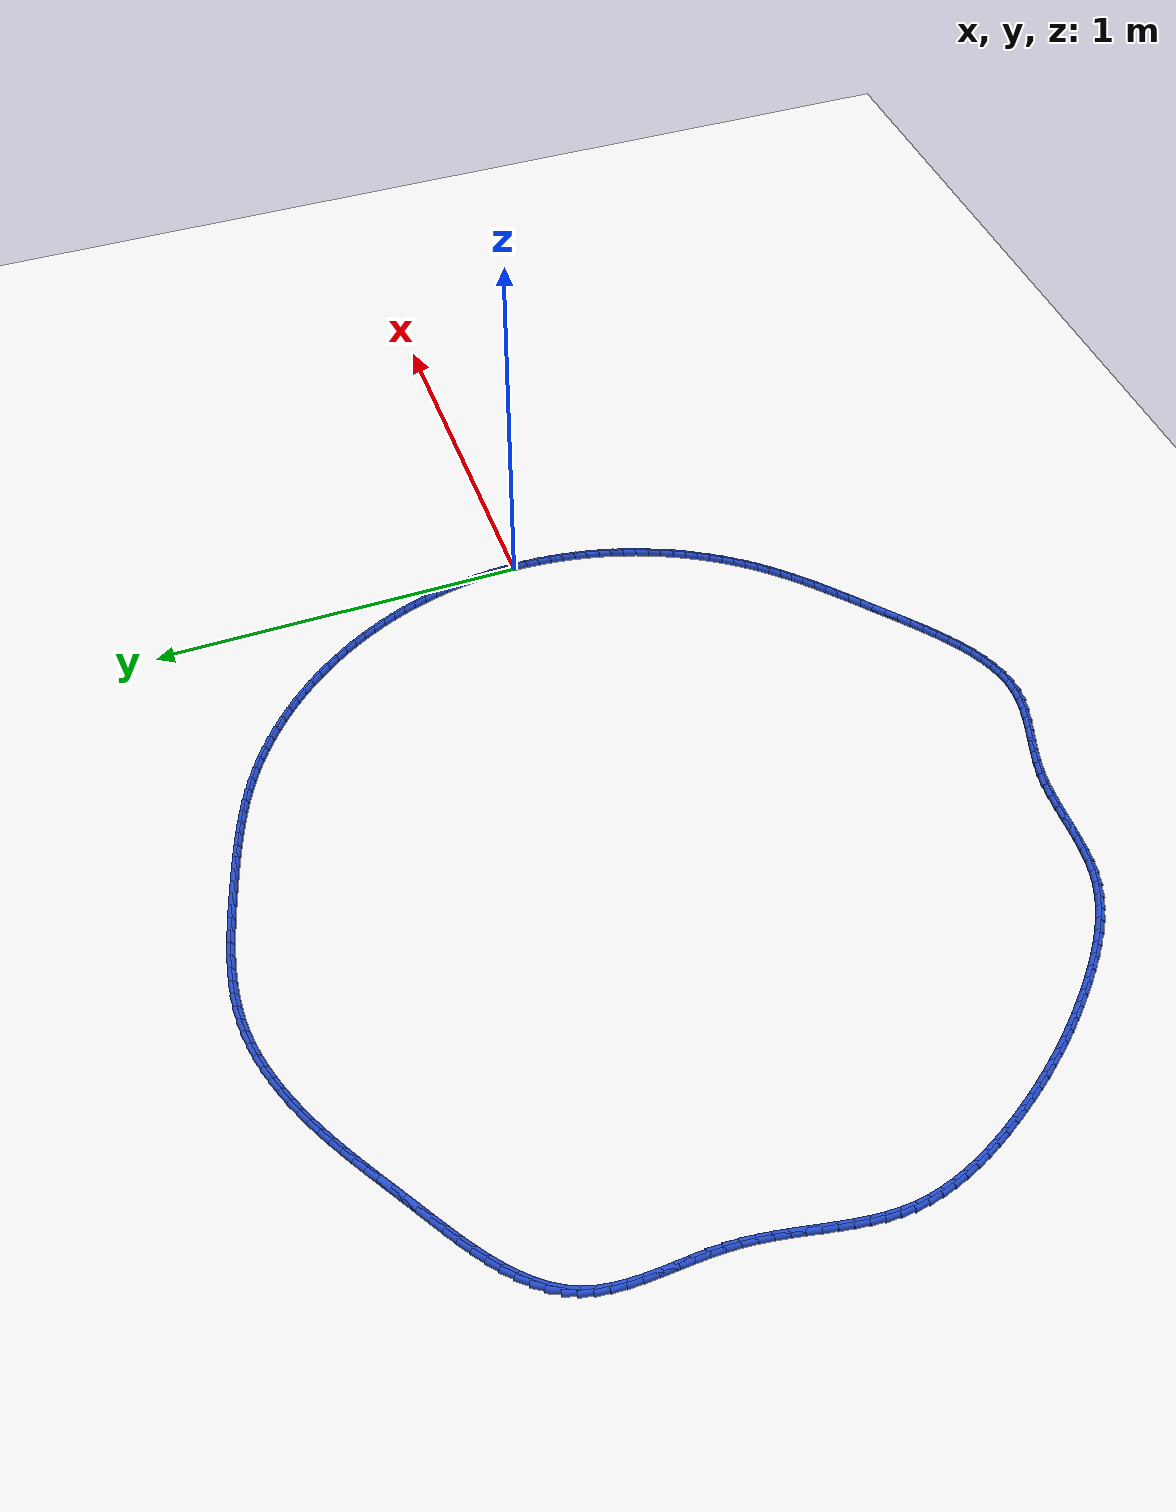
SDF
<sdf version="1.6">
 <world name="default">
  <light name="sun" type="directional">
   <pose>0 0 10 0 -0 0</pose>
   <diffuse>0.8 0.8 0.8 1</diffuse>
   <specular>0.2 0.2 0.2 1</specular>
   <attenuation>
    <range>1000</range>
    <constant>0.9</constant>
    <linear>0.01</linear>
    <quadratic>0.001</quadratic>
   </attenuation>
   <direction>-0.5 0.1 -0.9</direction>
  </light>
  <model name="ground_plane">
   <static>1</static>
   <link name="link">
    <collision name="collision">
     <geometry><plane><normal>0 0 1</normal><size>100 100</size></plane></geometry>
     <surface><friction><ode><mu>100</mu><mu2>50</mu2></ode></friction></surface>
    </collision>
    <visual name="visual">
     <cast_shadows>0</cast_shadows>
     <geometry><plane><normal>0 0 1</normal><size>100 100</size></plane></geometry>
     <material>
      <script><uri>file://media/materials/scripts/gazebo.material</uri><name>Gazebo/WhiteGlow</name></script>
     </material>
    </visual>
   </link>
  </model>
  <gravity>0 0 -9.8</gravity>
  <magnetic_field>6e-06 2.3e-05 -4.2e-05</magnetic_field>
  <atmosphere type="adiabatic"/>
  <physics name="default_physics" default="0" type="ode">
   <max_step_size>0.001</max_step_size>
   <real_time_factor>1</real_time_factor>
   <real_time_update_rate>1000</real_time_update_rate>
  </physics>
  <scene><ambient>0.4 0.4 0.4 1</ambient><background>0.7 0.7 0.7 1</background><shadows>1</shadows></scene>
  <spherical_coordinates>
   <surface_model>EARTH_WGS84</surface_model>
   <latitude_deg>0</latitude_deg>
   <longitude_deg>0</longitude_deg>
   <elevation>0</elevation>
   <heading_deg>0</heading_deg>
  </spherical_coordinates>
  <model name="line">
   <link name="link_0">
    <pose>1.734723475976807e-18 9.71445146547012e-17 0.01 0 1.57 -1.5542168274850594</pose>
    <collision name="collision">
     <geometry><cylinder><radius>0.01</radius><length>0.08</length></cylinder></geometry>
    </collision>
    <visual name="visual">
     <material>
      <script><name>Gazebo/Blue</name><uri>file://media/materials/scripts/gazebo.material</uri></script>
     </material>
     <geometry><cylinder><radius>0.01</radius><length>0.08</length></cylinder></geometry>
    </visual>
   </link>
   <link name="link_1">
    <pose>-0.0005699413144302086 0.03437311833359964 0.01 0 1.57 -1.5199864834201993</pose>
    <collision name="collision">
     <geometry><cylinder><radius>0.01</radius><length>0.08</length></cylinder></geometry>
    </collision>
    <visual name="visual">
     <material>
      <script><name>Gazebo/Blue</name><uri>file://media/materials/scripts/gazebo.material</uri></script>
     </material>
     <geometry><cylinder><radius>0.01</radius><length>0.08</length></cylinder></geometry>
    </visual>
   </link>
   <link name="link_2">
    <pose>-0.0023165897945779503 0.0687197140490652 0.01 0 1.57 -1.485694874704262</pose>
    <collision name="collision">
     <geometry><cylinder><radius>0.01</radius><length>0.08</length></cylinder></geometry>
    </collision>
    <visual name="visual">
     <material>
      <script><name>Gazebo/Blue</name><uri>file://media/materials/scripts/gazebo.material</uri></script>
     </material>
     <geometry><cylinder><radius>0.01</radius><length>0.08</length></cylinder></geometry>
    </visual>
   </link>
   <link name="link_3">
    <pose>-0.005240828427916939 0.10299851644580163 0.01 0 1.57 -1.4512998003957758</pose>
    <collision name="collision">
     <geometry><cylinder><radius>0.01</radius><length>0.08</length></cylinder></geometry>
    </collision>
    <visual name="visual">
     <material>
      <script><name>Gazebo/Blue</name><uri>file://media/materials/scripts/gazebo.material</uri></script>
     </material>
     <geometry><cylinder><radius>0.01</radius><length>0.08</length></cylinder></geometry>
    </visual>
   </link>
   <link name="link_4">
    <pose>-0.009343540201920894 0.13716825482321376 0.01 0 1.57 -1.4167599571326206</pose>
    <collision name="collision">
     <geometry><cylinder><radius>0.01</radius><length>0.08</length></cylinder></geometry>
    </collision>
    <visual name="visual">
     <material>
      <script><name>Gazebo/Blue</name><uri>file://media/materials/scripts/gazebo.material</uri></script>
     </material>
     <geometry><cylinder><radius>0.01</radius><length>0.08</length></cylinder></geometry>
    </visual>
   </link>
   <link name="link_5">
    <pose>-0.01462560810406353 0.17118765848070652 0.01 0 1.57 -1.3820352444931414</pose>
    <collision name="collision">
     <geometry><cylinder><radius>0.01</radius><length>0.08</length></cylinder></geometry>
    </collision>
    <visual name="visual">
     <material>
      <script><name>Gazebo/Blue</name><uri>file://media/materials/scripts/gazebo.material</uri></script>
     </material>
     <geometry><cylinder><radius>0.01</radius><length>0.08</length></cylinder></geometry>
    </visual>
   </link>
   <link name="link_6">
    <pose>-0.021087915121818568 0.20501545671768473 0.01 0 1.57 -1.3470870885615318</pose>
    <collision name="collision">
     <geometry><cylinder><radius>0.01</radius><length>0.08</length></cylinder></geometry>
    </collision>
    <visual name="visual">
     <material>
      <script><name>Gazebo/Blue</name><uri>file://media/materials/scripts/gazebo.material</uri></script>
     </material>
     <geometry><cylinder><radius>0.01</radius><length>0.08</length></cylinder></geometry>
    </visual>
   </link>
   <link name="link_7">
    <pose>-0.028731344242659704 0.23861037883355316 0.01 0 1.57 -1.3118787876589248</pose>
    <collision name="collision">
     <geometry><cylinder><radius>0.01</radius><length>0.08</length></cylinder></geometry>
    </collision>
    <visual name="visual">
     <material>
      <script><name>Gazebo/Blue</name><uri>file://media/materials/scripts/gazebo.material</uri></script>
     </material>
     <geometry><cylinder><radius>0.01</radius><length>0.08</length></cylinder></geometry>
    </visual>
   </link>
   <link name="link_8">
    <pose>-0.03755677845406068 0.27193115412771673 0.01 0 1.57 -1.2763758832175205</pose>
    <collision name="collision">
     <geometry><cylinder><radius>0.01</radius><length>0.08</length></cylinder></geometry>
    </collision>
    <visual name="visual">
     <material>
      <script><name>Gazebo/Blue</name><uri>file://media/materials/scripts/gazebo.material</uri></script>
     </material>
     <geometry><cylinder><radius>0.01</radius><length>0.08</length></cylinder></geometry>
    </visual>
   </link>
   <link name="link_9">
    <pose>-0.0475651007434952 0.3049365118995803 0.01 0 1.57 -1.240554124326306</pose>
    <collision name="collision">
     <geometry><cylinder><radius>0.01</radius><length>0.08</length></cylinder></geometry>
    </collision>
    <visual name="visual">
     <material>
      <script><name>Gazebo/Blue</name><uri>file://media/materials/scripts/gazebo.material</uri></script>
     </material>
     <geometry><cylinder><radius>0.01</radius><length>0.08</length></cylinder></geometry>
    </visual>
   </link>
   <link name="link_10">
    <pose>-0.058756923608543905 0.3375851977467124 0.01 0 1.57 -1.2046821692691358</pose>
    <collision name="collision">
     <geometry><cylinder><radius>0.01</radius><length>0.08</length></cylinder></geometry>
    </collision>
    <visual name="visual">
     <material>
      <script><name>Gazebo/Blue</name><uri>file://media/materials/scripts/gazebo.material</uri></script>
     </material>
     <geometry><cylinder><radius>0.01</radius><length>0.08</length></cylinder></geometry>
    </visual>
   </link>
   <link name="link_11">
    <pose>-0.07112209562300975 0.36983660583876315 0.01 0 1.57 -1.169108550293276</pose>
    <collision name="collision">
     <geometry><cylinder><radius>0.01</radius><length>0.08</length></cylinder></geometry>
    </collision>
    <visual name="visual">
     <material>
      <script><name>Gazebo/Blue</name><uri>file://media/materials/scripts/gazebo.material</uri></script>
     </material>
     <geometry><cylinder><radius>0.01</radius><length>0.08</length></cylinder></geometry>
    </visual>
   </link>
   <link name="link_12">
    <pose>-0.08463633708232285 0.40165098163410373 0.01 0 1.57 -1.1338066439252668</pose>
    <collision name="collision">
     <geometry><cylinder><radius>0.01</radius><length>0.08</length></cylinder></geometry>
    </collision>
    <visual name="visual">
     <material>
      <script><name>Gazebo/Blue</name><uri>file://media/materials/scripts/gazebo.material</uri></script>
     </material>
     <geometry><cylinder><radius>0.01</radius><length>0.08</length></cylinder></geometry>
    </visual>
   </link>
   <link name="link_13">
    <pose>-0.09927440927955722 0.43298862837506635 0.01 0 1.57 -1.098721480478272</pose>
    <collision name="collision">
     <geometry><cylinder><radius>0.01</radius><length>0.08</length></cylinder></geometry>
    </collision>
    <visual name="visual">
     <material>
      <script><name>Gazebo/Blue</name><uri>file://media/materials/scripts/gazebo.material</uri></script>
     </material>
     <geometry><cylinder><radius>0.01</radius><length>0.08</length></cylinder></geometry>
    </visual>
   </link>
   <link name="link_14">
    <pose>-0.1150110735077868 0.46380984930398367 0.01 0 1.57 -1.0637969533205747</pose>
    <collision name="collision">
     <geometry><cylinder><radius>0.01</radius><length>0.08</length></cylinder></geometry>
    </collision>
    <visual name="visual">
     <material>
      <script><name>Gazebo/Blue</name><uri>file://media/materials/scripts/gazebo.material</uri></script>
     </material>
     <geometry><cylinder><radius>0.01</radius><length>0.08</length></cylinder></geometry>
    </visual>
   </link>
   <link name="link_15">
    <pose>-0.1318210910600857 0.4940749476631881 0.01 0 1.57 -1.0289761606273053</pose>
    <collision name="collision">
     <geometry><cylinder><radius>0.01</radius><length>0.08</length></cylinder></geometry>
    </collision>
    <visual name="visual">
     <material>
      <script><name>Gazebo/Blue</name><uri>file://media/materials/scripts/gazebo.material</uri></script>
     </material>
     <geometry><cylinder><radius>0.01</radius><length>0.08</length></cylinder></geometry>
    </visual>
   </link>
   <link name="link_16">
    <pose>-0.14967922322952787 0.523744226695012 0.01 0 1.57 -0.9942017174378756</pose>
    <collision name="collision">
     <geometry><cylinder><radius>0.01</radius><length>0.08</length></cylinder></geometry>
    </collision>
    <visual name="visual">
     <material>
      <script><name>Gazebo/Blue</name><uri>file://media/materials/scripts/gazebo.material</uri></script>
     </material>
     <geometry><cylinder><radius>0.01</radius><length>0.08</length></cylinder></geometry>
    </visual>
   </link>
   <link name="link_17">
    <pose>-0.16856023130918737 0.5527779896417879 0.01 0 1.57 -0.9594160484844179</pose>
    <collision name="collision">
     <geometry><cylinder><radius>0.01</radius><length>0.08</length></cylinder></geometry>
    </collision>
    <visual name="visual">
     <material>
      <script><name>Gazebo/Blue</name><uri>file://media/materials/scripts/gazebo.material</uri></script>
     </material>
     <geometry><cylinder><radius>0.01</radius><length>0.08</length></cylinder></geometry>
    </visual>
   </link>
   <link name="link_18">
    <pose>-0.18843887659213815 0.581136539745848 0.01 0 1.57 -0.9245616724993994</pose>
    <collision name="collision">
     <geometry><cylinder><radius>0.01</radius><length>0.08</length></cylinder></geometry>
    </collision>
    <visual name="visual">
     <material>
      <script><name>Gazebo/Blue</name><uri>file://media/materials/scripts/gazebo.material</uri></script>
     </material>
     <geometry><cylinder><radius>0.01</radius><length>0.08</length></cylinder></geometry>
    </visual>
   </link>
   <link name="link_19">
    <pose>-0.2092899203714542 0.6087801802495251 0.01 0 1.57 -0.8895814887936446</pose>
    <collision name="collision">
     <geometry><cylinder><radius>0.01</radius><length>0.08</length></cylinder></geometry>
    </collision>
    <visual name="visual">
     <material>
      <script><name>Gazebo/Blue</name><uri>file://media/materials/scripts/gazebo.material</uri></script>
     </material>
     <geometry><cylinder><radius>0.01</radius><length>0.08</length></cylinder></geometry>
    </visual>
   </link>
   <link name="link_20">
    <pose>-0.23108812394020967 0.6356692143951516 0.01 0 1.57 -0.8544190768408078</pose>
    <collision name="collision">
     <geometry><cylinder><radius>0.01</radius><length>0.08</length></cylinder></geometry>
    </collision>
    <visual name="visual">
     <material>
      <script><name>Gazebo/Blue</name><uri>file://media/materials/scripts/gazebo.material</uri></script>
     </material>
     <geometry><cylinder><radius>0.01</radius><length>0.08</length></cylinder></geometry>
    </visual>
   </link>
   <link name="link_21">
    <pose>-0.2538082485914784 0.6617639454250592 0.01 0 1.57 -0.8190190194039858</pose>
    <collision name="collision">
     <geometry><cylinder><radius>0.01</radius><length>0.08</length></cylinder></geometry>
    </collision>
    <visual name="visual">
     <material>
      <script><name>Gazebo/Blue</name><uri>file://media/materials/scripts/gazebo.material</uri></script>
     </material>
     <geometry><cylinder><radius>0.01</radius><length>0.08</length></cylinder></geometry>
    </visual>
   </link>
   <link name="link_22">
    <pose>-0.2774250556183345 0.6870246765815813 0.01 0 1.57 -0.783327259362871</pose>
    <collision name="collision">
     <geometry><cylinder><radius>0.01</radius><length>0.08</length></cylinder></geometry>
    </collision>
    <visual name="visual">
     <material>
      <script><name>Gazebo/Blue</name><uri>file://media/materials/scripts/gazebo.material</uri></script>
     </material>
     <geometry><cylinder><radius>0.01</radius><length>0.08</length></cylinder></geometry>
    </visual>
   </link>
   <link name="link_23">
    <pose>-0.30191330631385205 0.7114117111070501 0.01 0 1.57 -0.7472765176907674</pose>
    <collision name="collision">
     <geometry><cylinder><radius>0.01</radius><length>0.08</length></cylinder></geometry>
    </collision>
    <visual name="visual">
     <material>
      <script><name>Gazebo/Blue</name><uri>file://media/materials/scripts/gazebo.material</uri></script>
     </material>
     <geometry><cylinder><radius>0.01</radius><length>0.08</length></cylinder></geometry>
    </visual>
   </link>
   <link name="link_24">
    <pose>-0.32724663166815404 0.7348835995864016 0.01 0 1.57 -0.7107102129986699</pose>
    <collision name="collision">
     <geometry><cylinder><radius>0.01</radius><length>0.08</length></cylinder></geometry>
    </collision>
    <visual name="visual">
     <material>
      <script><name>Gazebo/Blue</name><uri>file://media/materials/scripts/gazebo.material</uri></script>
     </material>
     <geometry><cylinder><radius>0.01</radius><length>0.08</length></cylinder></geometry>
    </visual>
   </link>
   <link name="link_25">
    <pose>-0.35339205602547213 0.7573886482831051 0.01 0 1.57 -0.6734958401632576</pose>
    <collision name="collision">
     <geometry><cylinder><radius>0.01</radius><length>0.08</length></cylinder></geometry>
    </collision>
    <visual name="visual">
     <material>
      <script><name>Gazebo/Blue</name><uri>file://media/materials/scripts/gazebo.material</uri></script>
     </material>
     <geometry><cylinder><radius>0.01</radius><length>0.08</length></cylinder></geometry>
    </visual>
   </link>
   <link name="link_26">
    <pose>-0.38031421034018076 0.7788714522499031 0.01 0 1.57 -0.6355304671792799</pose>
    <collision name="collision">
     <geometry><cylinder><radius>0.01</radius><length>0.08</length></cylinder></geometry>
    </collision>
    <visual name="visual">
     <material>
      <script><name>Gazebo/Blue</name><uri>file://media/materials/scripts/gazebo.material</uri></script>
     </material>
     <geometry><cylinder><radius>0.01</radius><length>0.08</length></cylinder></geometry>
    </visual>
   </link>
   <link name="link_27">
    <pose>-0.40797772224425355 0.799276601387796 0.01 0 1.57 -0.5967143540920707</pose>
    <collision name="collision">
     <geometry><cylinder><radius>0.01</radius><length>0.08</length></cylinder></geometry>
    </collision>
    <visual name="visual">
     <material>
      <script><name>Gazebo/Blue</name><uri>file://media/materials/scripts/gazebo.material</uri></script>
     </material>
     <geometry><cylinder><radius>0.01</radius><length>0.08</length></cylinder></geometry>
    </visual>
   </link>
   <link name="link_28">
    <pose>-0.43634721936966486 0.8185486855977848 0.01 0 1.57 -0.5569519282279846</pose>
    <collision name="collision">
     <geometry><cylinder><radius>0.01</radius><length>0.08</length></cylinder></geometry>
    </collision>
    <visual name="visual">
     <material>
      <script><name>Gazebo/Blue</name><uri>file://media/materials/scripts/gazebo.material</uri></script>
     </material>
     <geometry><cylinder><radius>0.01</radius><length>0.08</length></cylinder></geometry>
    </visual>
   </link>
   <link name="link_29">
    <pose>-0.465387329348389 0.8366322947808702 0.01 0 1.57 -0.5161844385838655</pose>
    <collision name="collision">
     <geometry><cylinder><radius>0.01</radius><length>0.08</length></cylinder></geometry>
    </collision>
    <visual name="visual">
     <material>
      <script><name>Gazebo/Blue</name><uri>file://media/materials/scripts/gazebo.material</uri></script>
     </material>
     <geometry><cylinder><radius>0.01</radius><length>0.08</length></cylinder></geometry>
    </visual>
   </link>
   <link name="link_30">
    <pose>-0.4950625956150744 0.8534731996230657 0.01 0 1.57 -0.4760872589783241</pose>
    <collision name="collision">
     <geometry><cylinder><radius>0.01</radius><length>0.08</length></cylinder></geometry>
    </collision>
    <visual name="visual">
     <material>
      <script><name>Gazebo/Blue</name><uri>file://media/materials/scripts/gazebo.material</uri></script>
     </material>
     <geometry><cylinder><radius>0.01</radius><length>0.08</length></cylinder></geometry>
    </visual>
   </link>
   <link name="link_31">
    <pose>-0.5253329366530195 0.869082031222541 0.01 0 1.57 -0.43936023849952954</pose>
    <collision name="collision">
     <geometry><cylinder><radius>0.01</radius><length>0.08</length></cylinder></geometry>
    </collision>
    <visual name="visual">
     <material>
      <script><name>Gazebo/Blue</name><uri>file://media/materials/scripts/gazebo.material</uri></script>
     </material>
     <geometry><cylinder><radius>0.01</radius><length>0.08</length></cylinder></geometry>
    </visual>
   </link>
   <link name="link_32">
    <pose>-0.5561513375172285 0.8835666552174195 0.01 0 1.57 -0.4063447480765154</pose>
    <collision name="collision">
     <geometry><cylinder><radius>0.01</radius><length>0.08</length></cylinder></geometry>
    </collision>
    <visual name="visual">
     <material>
      <script><name>Gazebo/Blue</name><uri>file://media/materials/scripts/gazebo.material</uri></script>
     </material>
     <geometry><cylinder><radius>0.01</radius><length>0.08</length></cylinder></geometry>
    </visual>
   </link>
   <link name="link_33">
    <pose>-0.5874702135108187 0.8970429274579074 0.01 0 1.57 -0.3771120335657032</pose>
    <collision name="collision">
     <geometry><cylinder><radius>0.01</radius><length>0.08</length></cylinder></geometry>
    </collision>
    <visual name="visual">
     <material>
      <script><name>Gazebo/Blue</name><uri>file://media/materials/scripts/gazebo.material</uri></script>
     </material>
     <geometry><cylinder><radius>0.01</radius><length>0.08</length></cylinder></geometry>
    </visual>
   </link>
   <link name="link_34">
    <pose>-0.6192419799369085 0.9096267037942112 0.01 0 1.57 -0.35168794315972185</pose>
    <collision name="collision">
     <geometry><cylinder><radius>0.01</radius><length>0.08</length></cylinder></geometry>
    </collision>
    <visual name="visual">
     <material>
      <script><name>Gazebo/Blue</name><uri>file://media/materials/scripts/gazebo.material</uri></script>
     </material>
     <geometry><cylinder><radius>0.01</radius><length>0.08</length></cylinder></geometry>
    </visual>
   </link>
   <link name="link_35">
    <pose>-0.6514190520986154 0.9214338400765382 0.01 0 1.57 -0.3300653692220338</pose>
    <collision name="collision">
     <geometry><cylinder><radius>0.01</radius><length>0.08</length></cylinder></geometry>
    </collision>
    <visual name="visual">
     <material>
      <script><name>Gazebo/Blue</name><uri>file://media/materials/scripts/gazebo.material</uri></script>
     </material>
     <geometry><cylinder><radius>0.01</radius><length>0.08</length></cylinder></geometry>
    </visual>
   </link>
   <link name="link_36">
    <pose>-0.6839538452990572 0.9325801921550945 0.01 0 1.57 -0.31221543487642933</pose>
    <collision name="collision">
     <geometry><cylinder><radius>0.01</radius><length>0.08</length></cylinder></geometry>
    </collision>
    <visual name="visual">
     <material>
      <script><name>Gazebo/Blue</name><uri>file://media/materials/scripts/gazebo.material</uri></script>
     </material>
     <geometry><cylinder><radius>0.01</radius><length>0.08</length></cylinder></geometry>
    </visual>
   </link>
   <link name="link_37">
    <pose>-0.7167987748413518 0.943181615880087 0.01 0 1.57 -0.2980969697529193</pose>
    <collision name="collision">
     <geometry><cylinder><radius>0.01</radius><length>0.08</length></cylinder></geometry>
    </collision>
    <visual name="visual">
     <material>
      <script><name>Gazebo/Blue</name><uri>file://media/materials/scripts/gazebo.material</uri></script>
     </material>
     <geometry><cylinder><radius>0.01</radius><length>0.08</length></cylinder></geometry>
    </visual>
   </link>
   <link name="link_38">
    <pose>-0.7499062560286164 0.9533539671017218 0.01 0 1.57 -0.28766411263076835</pose>
    <collision name="collision">
     <geometry><cylinder><radius>0.01</radius><length>0.08</length></cylinder></geometry>
    </collision>
    <visual name="visual">
     <material>
      <script><name>Gazebo/Blue</name><uri>file://media/materials/scripts/gazebo.material</uri></script>
     </material>
     <geometry><cylinder><radius>0.01</radius><length>0.08</length></cylinder></geometry>
    </visual>
   </link>
   <link name="link_39">
    <pose>-0.7832287041639696 0.963213101670206 0.01 0 1.57 -0.28083087801892254</pose>
    <collision name="collision">
     <geometry><cylinder><radius>0.01</radius><length>0.08</length></cylinder></geometry>
    </collision>
    <visual name="visual">
     <material>
      <script><name>Gazebo/Blue</name><uri>file://media/materials/scripts/gazebo.material</uri></script>
     </material>
     <geometry><cylinder><radius>0.01</radius><length>0.08</length></cylinder></geometry>
    </visual>
   </link>
   <link name="link_40">
    <pose>-0.8167186772635532 0.9728734224620671 0.01 0 1.57 -0.27450820406204046</pose>
    <collision name="collision">
     <geometry><cylinder><radius>0.01</radius><length>0.08</length></cylinder></geometry>
    </collision>
    <visual name="visual">
     <material>
      <script><name>Gazebo/Blue</name><uri>file://media/materials/scripts/gazebo.material</uri></script>
     </material>
     <geometry><cylinder><radius>0.01</radius><length>0.08</length></cylinder></geometry>
    </visual>
   </link>
   <link name="link_41">
    <pose>-0.8503393158635872 0.9823415907989572 0.01 0 1.57 -0.26357270714695774</pose>
    <collision name="collision">
     <geometry><cylinder><radius>0.01</radius><length>0.08</length></cylinder></geometry>
    </collision>
    <visual name="visual">
     <material>
      <script><name>Gazebo/Blue</name><uri>file://media/materials/scripts/gazebo.material</uri></script>
     </material>
     <geometry><cylinder><radius>0.01</radius><length>0.08</length></cylinder></geometry>
    </visual>
   </link>
   <link name="link_42">
    <pose>-0.884071444034229 0.991444230409597 0.01 0 1.57 -0.24748363059681194</pose>
    <collision name="collision">
     <geometry><cylinder><radius>0.01</radius><length>0.08</length></cylinder></geometry>
    </collision>
    <visual name="visual">
     <material>
      <script><name>Gazebo/Blue</name><uri>file://media/materials/scripts/gazebo.material</uri></script>
     </material>
     <geometry><cylinder><radius>0.01</radius><length>0.08</length></cylinder></geometry>
    </visual>
   </link>
   <link name="link_43">
    <pose>-0.917897567203002 0.999990846977508 0.01 0 1.57 -0.22613830442118382</pose>
    <collision name="collision">
     <geometry><cylinder><radius>0.01</radius><length>0.08</length></cylinder></geometry>
    </collision>
    <visual name="visual">
     <material>
      <script><name>Gazebo/Blue</name><uri>file://media/materials/scripts/gazebo.material</uri></script>
     </material>
     <geometry><cylinder><radius>0.01</radius><length>0.08</length></cylinder></geometry>
    </visual>
   </link>
   <link name="link_44">
    <pose>-0.9518001907974311 1.0077909461862145 0.01 0 1.57 -0.19939819341375972</pose>
    <collision name="collision">
     <geometry><cylinder><radius>0.01</radius><length>0.08</length></cylinder></geometry>
    </collision>
    <visual name="visual">
     <material>
      <script><name>Gazebo/Blue</name><uri>file://media/materials/scripts/gazebo.material</uri></script>
     </material>
     <geometry><cylinder><radius>0.01</radius><length>0.08</length></cylinder></geometry>
    </visual>
   </link>
   <link name="link_45">
    <pose>-0.985761820245039 1.0146540337192385 0.01 0 1.57 -0.16710500320656313</pose>
    <collision name="collision">
     <geometry><cylinder><radius>0.01</radius><length>0.08</length></cylinder></geometry>
    </collision>
    <visual name="visual">
     <material>
      <script><name>Gazebo/Blue</name><uri>file://media/materials/scripts/gazebo.material</uri></script>
     </material>
     <geometry><cylinder><radius>0.01</radius><length>0.08</length></cylinder></geometry>
    </visual>
   </link>
   <link name="link_46">
    <pose>-1.0197649609733506 1.0203896152601035 0.01 0 1.57 -0.12910306802618346</pose>
    <collision name="collision">
     <geometry><cylinder><radius>0.01</radius><length>0.08</length></cylinder></geometry>
    </collision>
    <visual name="visual">
     <material>
      <script><name>Gazebo/Blue</name><uri>file://media/materials/scripts/gazebo.material</uri></script>
     </material>
     <geometry><cylinder><radius>0.01</radius><length>0.08</length></cylinder></geometry>
    </visual>
   </link>
   <link name="link_47">
    <pose>-1.053792118409889 1.024807196492332 0.01 0 1.57 -0.08526943565933354</pose>
    <collision name="collision">
     <geometry><cylinder><radius>0.01</radius><length>0.08</length></cylinder></geometry>
    </collision>
    <visual name="visual">
     <material>
      <script><name>Gazebo/Blue</name><uri>file://media/materials/scripts/gazebo.material</uri></script>
     </material>
     <geometry><cylinder><radius>0.01</radius><length>0.08</length></cylinder></geometry>
    </visual>
   </link>
   <link name="link_48">
    <pose>-1.0878257979821788 1.0277162830994477 0.01 0 1.57 -0.035552367277115714</pose>
    <collision name="collision">
     <geometry><cylinder><radius>0.01</radius><length>0.08</length></cylinder></geometry>
    </collision>
    <visual name="visual">
     <material>
      <script><name>Gazebo/Blue</name><uri>file://media/materials/scripts/gazebo.material</uri></script>
     </material>
     <geometry><cylinder><radius>0.01</radius><length>0.08</length></cylinder></geometry>
    </visual>
   </link>
   <link name="link_49">
    <pose>-1.1218485051177431 1.0289263807649724 0.01 0 1.57 0.019982654706154315</pose>
    <collision name="collision">
     <geometry><cylinder><radius>0.01</radius><length>0.08</length></cylinder></geometry>
    </collision>
    <visual name="visual">
     <material>
      <script><name>Gazebo/Blue</name><uri>file://media/materials/scripts/gazebo.material</uri></script>
     </material>
     <geometry><cylinder><radius>0.01</radius><length>0.08</length></cylinder></geometry>
    </visual>
   </link>
   <link name="link_50">
    <pose>-1.1558427452441067 1.02824699517243 0.01 0 1.57 0.08109651236743927</pose>
    <collision name="collision">
     <geometry><cylinder><radius>0.01</radius><length>0.08</length></cylinder></geometry>
    </collision>
    <visual name="visual">
     <material>
      <script><name>Gazebo/Blue</name><uri>file://media/materials/scripts/gazebo.material</uri></script>
     </material>
     <geometry><cylinder><radius>0.01</radius><length>0.08</length></cylinder></geometry>
    </visual>
   </link>
   <link name="link_51">
    <pose>-1.189790971372887 1.0254878611643579 0.01 0 1.57 0.14460756494542634</pose>
    <collision name="collision">
     <geometry><cylinder><radius>0.01</radius><length>0.08</length></cylinder></geometry>
    </collision>
    <visual name="visual">
     <material>
      <script><name>Gazebo/Blue</name><uri>file://media/materials/scripts/gazebo.material</uri></script>
     </material>
     <geometry><cylinder><radius>0.01</radius><length>0.08</length></cylinder></geometry>
    </visual>
   </link>
   <link name="link_52">
    <pose>-1.2236532232462742 1.0205567029755032 0.01 0 1.57 0.2033703355167204</pose>
    <collision name="collision">
     <geometry><cylinder><radius>0.01</radius><length>0.08</length></cylinder></geometry>
    </collision>
    <visual name="visual">
     <material>
      <script><name>Gazebo/Blue</name><uri>file://media/materials/scripts/gazebo.material</uri></script>
     </material>
     <geometry><cylinder><radius>0.01</radius><length>0.08</length></cylinder></geometry>
    </visual>
   </link>
   <link name="link_53">
    <pose>-1.257332332721897 1.0136113540830571 0.01 0 1.57 0.25663979868975917</pose>
    <collision name="collision">
     <geometry><cylinder><radius>0.01</radius><length>0.08</length></cylinder></geometry>
    </collision>
    <visual name="visual">
     <material>
      <script><name>Gazebo/Blue</name><uri>file://media/materials/scripts/gazebo.material</uri></script>
     </material>
     <geometry><cylinder><radius>0.01</radius><length>0.08</length></cylinder></geometry>
    </visual>
   </link>
   <link name="link_54">
    <pose>-1.290722135949428 1.0048489766287825 0.01 0 1.57 0.3048582976706738</pose>
    <collision name="collision">
     <geometry><cylinder><radius>0.01</radius><length>0.08</length></cylinder></geometry>
    </collision>
    <visual name="visual">
     <material>
      <script><name>Gazebo/Blue</name><uri>file://media/materials/scripts/gazebo.material</uri></script>
     </material>
     <geometry><cylinder><radius>0.01</radius><length>0.08</length></cylinder></geometry>
    </visual>
   </link>
   <link name="link_55">
    <pose>-1.3237164690785381 0.9944667327544424 0.01 0 1.57 0.34848342156612244</pose>
    <collision name="collision">
     <geometry><cylinder><radius>0.01</radius><length>0.08</length></cylinder></geometry>
    </collision>
    <visual name="visual">
     <material>
      <script><name>Gazebo/Blue</name><uri>file://media/materials/scripts/gazebo.material</uri></script>
     </material>
     <geometry><cylinder><radius>0.01</radius><length>0.08</length></cylinder></geometry>
    </visual>
   </link>
   <link name="link_56">
    <pose>-1.3562091682588984 0.9826617846018001 0.01 0 1.57 0.38796045394522594</pose>
    <collision name="collision">
     <geometry><cylinder><radius>0.01</radius><length>0.08</length></cylinder></geometry>
    </collision>
    <visual name="visual">
     <material>
      <script><name>Gazebo/Blue</name><uri>file://media/materials/scripts/gazebo.material</uri></script>
     </material>
     <geometry><cylinder><radius>0.01</radius><length>0.08</length></cylinder></geometry>
    </visual>
   </link>
   <link name="link_57">
    <pose>-1.3880940696401807 0.9696312943126184 0.01 0 1.57 0.4237067378511953</pose>
    <collision name="collision">
     <geometry><cylinder><radius>0.01</radius><length>0.08</length></cylinder></geometry>
    </collision>
    <visual name="visual">
     <material>
      <script><name>Gazebo/Blue</name><uri>file://media/materials/scripts/gazebo.material</uri></script>
     </material>
     <geometry><cylinder><radius>0.01</radius><length>0.08</length></cylinder></geometry>
    </visual>
   </link>
   <link name="link_58">
    <pose>-1.4192659630576607 0.9555719630279014 0.01 0 1.57 0.45608189640159075</pose>
    <collision name="collision">
     <geometry><cylinder><radius>0.01</radius><length>0.08</length></cylinder></geometry>
    </collision>
    <visual name="visual">
     <material>
      <script><name>Gazebo/Blue</name><uri>file://media/materials/scripts/gazebo.material</uri></script>
     </material>
     <geometry><cylinder><radius>0.01</radius><length>0.08</length></cylinder></geometry>
    </visual>
   </link>
   <link name="link_59">
    <pose>-1.4497053302204466 0.9406390694128214 0.01 0 1.57 0.48499546415280004</pose>
    <collision name="collision">
     <geometry><cylinder><radius>0.01</radius><length>0.08</length></cylinder></geometry>
    </collision>
    <visual name="visual">
     <material>
      <script><name>Gazebo/Blue</name><uri>file://media/materials/scripts/gazebo.material</uri></script>
     </material>
     <geometry><cylinder><radius>0.01</radius><length>0.08</length></cylinder></geometry>
    </visual>
   </link>
   <link name="link_60">
    <pose>-1.4795451030825684 0.9249141994204763 0.01 0 1.57 0.5101026659063499</pose>
    <collision name="collision">
     <geometry><cylinder><radius>0.01</radius><length>0.08</length></cylinder></geometry>
    </collision>
    <visual name="visual">
     <material>
      <script><name>Gazebo/Blue</name><uri>file://media/materials/scripts/gazebo.material</uri></script>
     </material>
     <geometry><cylinder><radius>0.01</radius><length>0.08</length></cylinder></geometry>
    </visual>
   </link>
   <link name="link_61">
    <pose>-1.5089339243716522 0.9084713445949403 0.01 0 1.57 0.5311398442823968</pose>
    <collision name="collision">
     <geometry><cylinder><radius>0.01</radius><length>0.08</length></cylinder></geometry>
    </collision>
    <visual name="visual">
     <material>
      <script><name>Gazebo/Blue</name><uri>file://media/materials/scripts/gazebo.material</uri></script>
     </material>
     <geometry><cylinder><radius>0.01</radius><length>0.08</length></cylinder></geometry>
    </visual>
   </link>
   <link name="link_62">
    <pose>-1.5380204368153285 0.8913844964802894 0.01 0 1.57 0.5479368123841477</pose>
    <collision name="collision">
     <geometry><cylinder><radius>0.01</radius><length>0.08</length></cylinder></geometry>
    </collision>
    <visual name="visual">
     <material>
      <script><name>Gazebo/Blue</name><uri>file://media/materials/scripts/gazebo.material</uri></script>
     </material>
     <geometry><cylinder><radius>0.01</radius><length>0.08</length></cylinder></geometry>
    </visual>
   </link>
   <link name="link_63">
    <pose>-1.5669532831412245 0.8737276466205984 0.01 0 1.57 0.5604111990578643</pose>
    <collision name="collision">
     <geometry><cylinder><radius>0.01</radius><length>0.08</length></cylinder></geometry>
    </collision>
    <visual name="visual">
     <material>
      <script><name>Gazebo/Blue</name><uri>file://media/materials/scripts/gazebo.material</uri></script>
     </material>
     <geometry><cylinder><radius>0.01</radius><length>0.08</length></cylinder></geometry>
    </visual>
   </link>
   <link name="link_64">
    <pose>-1.5958811060769706 0.8555747865599422 0.01 0 1.57 0.5685601439831506</pose>
    <collision name="collision">
     <geometry><cylinder><radius>0.01</radius><length>0.08</length></cylinder></geometry>
    </collision>
    <visual name="visual">
     <material>
      <script><name>Gazebo/Blue</name><uri>file://media/materials/scripts/gazebo.material</uri></script>
     </material>
     <geometry><cylinder><radius>0.01</radius><length>0.08</length></cylinder></geometry>
    </visual>
   </link>
   <link name="link_65">
    <pose>-1.6249525483501945 0.836999907842396 0.01 0 1.57 0.5724509035087524</pose>
    <collision name="collision">
     <geometry><cylinder><radius>0.01</radius><length>0.08</length></cylinder></geometry>
    </collision>
    <visual name="visual">
     <material>
      <script><name>Gazebo/Blue</name><uri>file://media/materials/scripts/gazebo.material</uri></script>
     </material>
     <geometry><cylinder><radius>0.01</radius><length>0.08</length></cylinder></geometry>
    </visual>
   </link>
   <link name="link_66">
    <pose>-1.6543162526885247 0.8180770020120348 0.01 0 1.57 0.5722114882028336</pose>
    <collision name="collision">
     <geometry><cylinder><radius>0.01</radius><length>0.08</length></cylinder></geometry>
    </collision>
    <visual name="visual">
     <material>
      <script><name>Gazebo/Blue</name><uri>file://media/materials/scripts/gazebo.material</uri></script>
     </material>
     <geometry><cylinder><radius>0.01</radius><length>0.08</length></cylinder></geometry>
    </visual>
   </link>
   <link name="link_67">
    <pose>-1.6841208618195904 0.7988800606129335 0.01 0 1.57 0.5682456371189241</pose>
    <collision name="collision">
     <geometry><cylinder><radius>0.01</radius><length>0.08</length></cylinder></geometry>
    </collision>
    <visual name="visual">
     <material>
      <script><name>Gazebo/Blue</name><uri>file://media/materials/scripts/gazebo.material</uri></script>
     </material>
     <geometry><cylinder><radius>0.01</radius><length>0.08</length></cylinder></geometry>
    </visual>
   </link>
   <link name="link_68">
    <pose>-1.714505467488925 0.7794796052700265 0.01 0 1.57 0.5666664859572857</pose>
    <collision name="collision">
     <geometry><cylinder><radius>0.01</radius><length>0.08</length></cylinder></geometry>
    </collision>
    <visual name="visual">
     <material>
      <script><name>Gazebo/Blue</name><uri>file://media/materials/scripts/gazebo.material</uri></script>
     </material>
     <geometry><cylinder><radius>0.01</radius><length>0.08</length></cylinder></geometry>
    </visual>
   </link>
   <link name="link_69">
    <pose>-1.745351982641816 0.7598527232752468 0.01 0 1.57 0.573781540912842</pose>
    <collision name="collision">
     <geometry><cylinder><radius>0.01</radius><length>0.08</length></cylinder></geometry>
    </collision>
    <visual name="visual">
     <material>
      <script><name>Gazebo/Blue</name><uri>file://media/materials/scripts/gazebo.material</uri></script>
     </material>
     <geometry><cylinder><radius>0.01</radius><length>0.08</length></cylinder></geometry>
    </visual>
   </link>
   <link name="link_70">
    <pose>-1.7762623990714401 0.7398748051783551 0.01 0 1.57 0.5899005058462293</pose>
    <collision name="collision">
     <geometry><cylinder><radius>0.01</radius><length>0.08</length></cylinder></geometry>
    </collision>
    <visual name="visual">
     <material>
      <script><name>Gazebo/Blue</name><uri>file://media/materials/scripts/gazebo.material</uri></script>
     </material>
     <geometry><cylinder><radius>0.01</radius><length>0.08</length></cylinder></geometry>
    </visual>
   </link>
   <link name="link_71">
    <pose>-1.8068245988780502 0.7194161154077297 0.01 0 1.57 0.6153923705280571</pose>
    <collision name="collision">
     <geometry><cylinder><radius>0.01</radius><length>0.08</length></cylinder></geometry>
    </collision>
    <visual name="visual">
     <material>
      <script><name>Gazebo/Blue</name><uri>file://media/materials/scripts/gazebo.material</uri></script>
     </material>
     <geometry><cylinder><radius>0.01</radius><length>0.08</length></cylinder></geometry>
    </visual>
   </link>
   <link name="link_72">
    <pose>-1.8366264641618983 0.6983469183917485 0.01 0 1.57 0.6510005567711977</pose>
    <collision name="collision">
     <geometry><cylinder><radius>0.01</radius><length>0.08</length></cylinder></geometry>
    </collision>
    <visual name="visual">
     <material>
      <script><name>Gazebo/Blue</name><uri>file://media/materials/scripts/gazebo.material</uri></script>
     </material>
     <geometry><cylinder><radius>0.01</radius><length>0.08</length></cylinder></geometry>
    </visual>
   </link>
   <link name="link_73">
    <pose>-1.865255877023238 0.6765374785587899 0.01 0 1.57 0.6978300374794848</pose>
    <collision name="collision">
     <geometry><cylinder><radius>0.01</radius><length>0.08</length></cylinder></geometry>
    </collision>
    <visual name="visual">
     <material>
      <script><name>Gazebo/Blue</name><uri>file://media/materials/scripts/gazebo.material</uri></script>
     </material>
     <geometry><cylinder><radius>0.01</radius><length>0.08</length></cylinder></geometry>
    </visual>
   </link>
   <link name="link_74">
    <pose>-1.8923007195623212 0.6538580603372315 0.01 0 1.57 0.7573099568522157</pose>
    <collision name="collision">
     <geometry><cylinder><radius>0.01</radius><length>0.08</length></cylinder></geometry>
    </collision>
    <visual name="visual">
     <material>
      <script><name>Gazebo/Blue</name><uri>file://media/materials/scripts/gazebo.material</uri></script>
     </material>
     <geometry><cylinder><radius>0.01</radius><length>0.08</length></cylinder></geometry>
    </visual>
   </link>
   <link name="link_75">
    <pose>-1.9173488738794011 0.6301789281554517 0.01 0 1.57 0.8310845415321725</pose>
    <collision name="collision">
     <geometry><cylinder><radius>0.01</radius><length>0.08</length></cylinder></geometry>
    </collision>
    <visual name="visual">
     <material>
      <script><name>Gazebo/Blue</name><uri>file://media/materials/scripts/gazebo.material</uri></script>
     </material>
     <geometry><cylinder><radius>0.01</radius><length>0.08</length></cylinder></geometry>
    </visual>
   </link>
   <link name="link_76">
    <pose>-1.9399882220747302 0.605370346441829 0.01 0 1.57 0.9207575955541076</pose>
    <collision name="collision">
     <geometry><cylinder><radius>0.01</radius><length>0.08</length></cylinder></geometry>
    </collision>
    <visual name="visual">
     <material>
      <script><name>Gazebo/Blue</name><uri>file://media/materials/scripts/gazebo.material</uri></script>
     </material>
     <geometry><cylinder><radius>0.01</radius><length>0.08</length></cylinder></geometry>
    </visual>
   </link>
   <link name="link_77">
    <pose>-1.9598066462485615 0.5793025796247409 0.01 0 1.57 1.0273996645319792</pose>
    <collision name="collision">
     <geometry><cylinder><radius>0.01</radius><length>0.08</length></cylinder></geometry>
    </collision>
    <visual name="visual">
     <material>
      <script><name>Gazebo/Blue</name><uri>file://media/materials/scripts/gazebo.material</uri></script>
     </material>
     <geometry><cylinder><radius>0.01</radius><length>0.08</length></cylinder></geometry>
    </visual>
   </link>
   <link name="link_78">
    <pose>-1.976392028501148 0.5518458921325656 0.01 0 1.57 1.1507764212607918</pose>
    <collision name="collision">
     <geometry><cylinder><radius>0.01</radius><length>0.08</length></cylinder></geometry>
    </collision>
    <visual name="visual">
     <material>
      <script><name>Gazebo/Blue</name><uri>file://media/materials/scripts/gazebo.material</uri></script>
     </material>
     <geometry><cylinder><radius>0.01</radius><length>0.08</length></cylinder></geometry>
    </visual>
   </link>
   <link name="link_79">
    <pose>-1.989332305351607 0.5228705662661953 0.01 0 1.57 1.2814644911011328</pose>
    <collision name="collision">
     <geometry><cylinder><radius>0.01</radius><length>0.08</length></cylinder></geometry>
    </collision>
    <visual name="visual">
     <material>
      <script><name>Gazebo/Blue</name><uri>file://media/materials/scripts/gazebo.material</uri></script>
     </material>
     <geometry><cylinder><radius>0.01</radius><length>0.08</length></cylinder></geometry>
    </visual>
   </link>
   <link name="link_80">
    <pose>-1.9984277633996574 0.49231662539423443 0.01 0 1.57 1.3929762045763714</pose>
    <collision name="collision">
     <geometry><cylinder><radius>0.01</radius><length>0.08</length></cylinder></geometry>
    </collision>
    <visual name="visual">
     <material>
      <script><name>Gazebo/Blue</name><uri>file://media/materials/scripts/gazebo.material</uri></script>
     </material>
     <geometry><cylinder><radius>0.01</radius><length>0.08</length></cylinder></geometry>
    </visual>
   </link>
   <link name="link_81">
    <pose>-2.004172406534245 0.4603519269614691 0.01 0 1.57 1.4796993411933885</pose>
    <collision name="collision">
     <geometry><cylinder><radius>0.01</radius><length>0.08</length></cylinder></geometry>
    </collision>
    <visual name="visual">
     <material>
      <script><name>Gazebo/Blue</name><uri>file://media/materials/scripts/gazebo.material</uri></script>
     </material>
     <geometry><cylinder><radius>0.01</radius><length>0.08</length></cylinder></geometry>
    </visual>
   </link>
   <link name="link_82">
    <pose>-2.007201671453798 0.42719077847813963 0.01 0 1.57 1.5429993904882124</pose>
    <collision name="collision">
     <geometry><cylinder><radius>0.01</radius><length>0.08</length></cylinder></geometry>
    </collision>
    <visual name="visual">
     <material>
      <script><name>Gazebo/Blue</name><uri>file://media/materials/scripts/gazebo.material</uri></script>
     </material>
     <geometry><cylinder><radius>0.01</radius><length>0.08</length></cylinder></geometry>
    </visual>
   </link>
   <link name="link_83">
    <pose>-2.008150994856745 0.3930474874544861 0.01 0 1.57 -1.5566132205159138</pose>
    <collision name="collision">
     <geometry><cylinder><radius>0.01</radius><length>0.08</length></cylinder></geometry>
    </collision>
    <visual name="visual">
     <material>
      <script><name>Gazebo/Blue</name><uri>file://media/materials/scripts/gazebo.material</uri></script>
     </material>
     <geometry><cylinder><radius>0.01</radius><length>0.08</length></cylinder></geometry>
    </visual>
   </link>
   <link name="link_84">
    <pose>-2.007655813441513 0.3581363614007472 0.01 0 1.57 -1.5340368524712304</pose>
    <collision name="collision">
     <geometry><cylinder><radius>0.01</radius><length>0.08</length></cylinder></geometry>
    </collision>
    <visual name="visual">
     <material>
      <script><name>Gazebo/Blue</name><uri>file://media/materials/scripts/gazebo.material</uri></script>
     </material>
     <geometry><cylinder><radius>0.01</radius><length>0.08</length></cylinder></geometry>
    </visual>
   </link>
   <link name="link_85">
    <pose>-2.0063515639065295 0.32267170782716303 0.01 0 1.57 -1.5295426207815475</pose>
    <collision name="collision">
     <geometry><cylinder><radius>0.01</radius><length>0.08</length></cylinder></geometry>
    </collision>
    <visual name="visual">
     <material>
      <script><name>Gazebo/Blue</name><uri>file://media/materials/scripts/gazebo.material</uri></script>
     </material>
     <geometry><cylinder><radius>0.01</radius><length>0.08</length></cylinder></geometry>
    </visual>
   </link>
   <link name="link_86">
    <pose>-2.004873682950222 0.28686783424397366 0.01 0 1.57 -1.5425235950090557</pose>
    <collision name="collision">
     <geometry><cylinder><radius>0.01</radius><length>0.08</length></cylinder></geometry>
    </collision>
    <visual name="visual">
     <material>
      <script><name>Gazebo/Blue</name><uri>file://media/materials/scripts/gazebo.material</uri></script>
     </material>
     <geometry><cylinder><radius>0.01</radius><length>0.08</length></cylinder></geometry>
    </visual>
   </link>
   <link name="link_87">
    <pose>-2.0038576072710192 0.25093904816141777 0.01 0 1.57 1.5685316075813471</pose>
    <collision name="collision">
     <geometry><cylinder><radius>0.01</radius><length>0.08</length></cylinder></geometry>
    </collision>
    <visual name="visual">
     <material>
      <script><name>Gazebo/Blue</name><uri>file://media/materials/scripts/gazebo.material</uri></script>
     </material>
     <geometry><cylinder><radius>0.01</radius><length>0.08</length></cylinder></geometry>
    </visual>
   </link>
   <link name="link_88">
    <pose>-2.0039387735673473 0.21509965708973564 0.01 0 1.57 1.520556298948108</pose>
    <collision name="collision">
     <geometry><cylinder><radius>0.01</radius><length>0.08</length></cylinder></geometry>
    </collision>
    <visual name="visual">
     <material>
      <script><name>Gazebo/Blue</name><uri>file://media/materials/scripts/gazebo.material</uri></script>
     </material>
     <geometry><cylinder><radius>0.01</radius><length>0.08</length></cylinder></geometry>
    </visual>
   </link>
   <link name="link_89">
    <pose>-2.005725910362969 0.17955762008579626 0.01 0 1.57 1.4694151996065563</pose>
    <collision name="collision">
     <geometry><cylinder><radius>0.01</radius><length>0.08</length></cylinder></geometry>
    </collision>
    <visual name="visual">
     <material>
      <script><name>Gazebo/Blue</name><uri>file://media/materials/scripts/gazebo.material</uri></script>
     </material>
     <geometry><cylinder><radius>0.01</radius><length>0.08</length></cylinder></geometry>
    </visual>
   </link>
   <link name="link_90">
    <pose>-2.009302884316126 0.14439613810821808 0.01 0 1.57 1.4289539555306998</pose>
    <collision name="collision">
     <geometry><cylinder><radius>0.01</radius><length>0.08</length></cylinder></geometry>
    </collision>
    <visual name="visual">
     <material>
      <script><name>Gazebo/Blue</name><uri>file://media/materials/scripts/gazebo.material</uri></script>
     </material>
     <geometry><cylinder><radius>0.01</radius><length>0.08</length></cylinder></geometry>
    </visual>
   </link>
   <link name="link_91">
    <pose>-2.014274042762086 0.10958443180434134 0.01 0 1.57 1.3999391413276476</pose>
    <collision name="collision">
     <geometry><cylinder><radius>0.01</radius><length>0.08</length></cylinder></geometry>
    </collision>
    <visual name="visual">
     <material>
      <script><name>Gazebo/Blue</name><uri>file://media/materials/scripts/gazebo.material</uri></script>
     </material>
     <geometry><cylinder><radius>0.01</radius><length>0.08</length></cylinder></geometry>
    </visual>
   </link>
   <link name="link_92">
    <pose>-2.0202261165828346 0.07508753444316311 0.01 0 1.57 1.38251317933754</pose>
    <collision name="collision">
     <geometry><cylinder><radius>0.01</radius><length>0.08</length></cylinder></geometry>
    </collision>
    <visual name="visual">
     <material>
      <script><name>Gazebo/Blue</name><uri>file://media/materials/scripts/gazebo.material</uri></script>
     </material>
     <geometry><cylinder><radius>0.01</radius><length>0.08</length></cylinder></geometry>
    </visual>
   </link>
   <link name="link_93">
    <pose>-2.0267458366603552 0.040870479293680456 0.01 0 1.57 1.376809106779105</pose>
    <collision name="collision">
     <geometry><cylinder><radius>0.01</radius><length>0.08</length></cylinder></geometry>
    </collision>
    <visual name="visual">
     <material>
      <script><name>Gazebo/Blue</name><uri>file://media/materials/scripts/gazebo.material</uri></script>
     </material>
     <geometry><cylinder><radius>0.01</radius><length>0.08</length></cylinder></geometry>
    </visual>
   </link>
   <link name="link_94">
    <pose>-2.0334199338766346 0.006898299624889243 0.01 0 1.57 1.3830236956044042</pose>
    <collision name="collision">
     <geometry><cylinder><radius>0.01</radius><length>0.08</length></cylinder></geometry>
    </collision>
    <visual name="visual">
     <material>
      <script><name>Gazebo/Blue</name><uri>file://media/materials/scripts/gazebo.material</uri></script>
     </material>
     <geometry><cylinder><radius>0.01</radius><length>0.08</length></cylinder></geometry>
    </visual>
   </link>
   <link name="link_95">
    <pose>-2.0398351391136553 -0.0268639712942135 0.01 0 1.57 1.4014456744473354</pose>
    <collision name="collision">
     <geometry><cylinder><radius>0.01</radius><length>0.08</length></cylinder></geometry>
    </collision>
    <visual name="visual">
     <material>
      <script><name>Gazebo/Blue</name><uri>file://media/materials/scripts/gazebo.material</uri></script>
     </material>
     <geometry><cylinder><radius>0.01</radius><length>0.08</length></cylinder></geometry>
    </visual>
   </link>
   <link name="link_96">
    <pose>-2.045578183253402 -0.0604513001946311 0.01 0 1.57 1.4324339924286216</pose>
    <collision name="collision">
     <geometry><cylinder><radius>0.01</radius><length>0.08</length></cylinder></geometry>
    </collision>
    <visual name="visual">
     <material>
      <script><name>Gazebo/Blue</name><uri>file://media/materials/scripts/gazebo.material</uri></script>
     </material>
     <geometry><cylinder><radius>0.01</radius><length>0.08</length></cylinder></geometry>
    </visual>
   </link>
   <link name="link_97">
    <pose>-2.050235797177862 -0.09389865380736692 0.01 0 1.57 1.4763364537004195</pose>
    <collision name="collision">
     <geometry><cylinder><radius>0.01</radius><length>0.08</length></cylinder></geometry>
    </collision>
    <visual name="visual">
     <material>
      <script><name>Gazebo/Blue</name><uri>file://media/materials/scripts/gazebo.material</uri></script>
     </material>
     <geometry><cylinder><radius>0.01</radius><length>0.08</length></cylinder></geometry>
    </visual>
   </link>
   <link name="link_98">
    <pose>-2.0533947117690188 -0.12724099886342355 0.01 0 1.57 1.5333368568740957</pose>
    <collision name="collision">
     <geometry><cylinder><radius>0.01</radius><length>0.08</length></cylinder></geometry>
    </collision>
    <visual name="visual">
     <material>
      <script><name>Gazebo/Blue</name><uri>file://media/materials/scripts/gazebo.material</uri></script>
     </material>
     <geometry><cylinder><radius>0.01</radius><length>0.08</length></cylinder></geometry>
    </visual>
   </link>
   <link name="link_99">
    <pose>-2.0546416579088564 -0.16051330209380577 0.01 0 1.57 -1.538365531827235</pose>
    <collision name="collision">
     <geometry><cylinder><radius>0.01</radius><length>0.08</length></cylinder></geometry>
    </collision>
    <visual name="visual">
     <material>
      <script><name>Gazebo/Blue</name><uri>file://media/materials/scripts/gazebo.material</uri></script>
     </material>
     <geometry><cylinder><radius>0.01</radius><length>0.08</length></cylinder></geometry>
    </visual>
   </link>
   <link name="link_100">
    <pose>-2.0535633701382863 -0.19375052964534217 0.01 0 1.57 -1.4599158488709547</pose>
    <collision name="collision">
     <geometry><cylinder><radius>0.01</radius><length>0.08</length></cylinder></geometry>
    </collision>
    <visual name="visual">
     <material>
      <script><name>Gazebo/Blue</name><uri>file://media/materials/scripts/gazebo.material</uri></script>
     </material>
     <geometry><cylinder><radius>0.01</radius><length>0.08</length></cylinder></geometry>
    </visual>
   </link>
   <link name="link_101">
    <pose>-2.049864948862996 -0.22696874969765618 0.01 0 1.57 -1.3863580437250722</pose>
    <collision name="collision">
     <geometry><cylinder><radius>0.01</radius><length>0.08</length></cylinder></geometry>
    </collision>
    <visual name="visual">
     <material>
      <script><name>Gazebo/Blue</name><uri>file://media/materials/scripts/gazebo.material</uri></script>
     </material>
     <geometry><cylinder><radius>0.01</radius><length>0.08</length></cylinder></geometry>
    </visual>
   </link>
   <link name="link_102">
    <pose>-2.043681153042575 -0.26011543233178325 0.01 0 1.57 -1.320544150617291</pose>
    <collision name="collision">
     <geometry><cylinder><radius>0.01</radius><length>0.08</length></cylinder></geometry>
    </collision>
    <visual name="visual">
     <material>
      <script><name>Gazebo/Blue</name><uri>file://media/materials/scripts/gazebo.material</uri></script>
     </material>
     <geometry><cylinder><radius>0.01</radius><length>0.08</length></cylinder></geometry>
    </visual>
   </link>
   <link name="link_103">
    <pose>-2.035244201307232 -0.2931224874867978 0.01 0 1.57 -1.2621418840904108</pose>
    <collision name="collision">
     <geometry><cylinder><radius>0.01</radius><length>0.08</length></cylinder></geometry>
    </collision>
    <visual name="visual">
     <material>
      <script><name>Gazebo/Blue</name><uri>file://media/materials/scripts/gazebo.material</uri></script>
     </material>
     <geometry><cylinder><radius>0.01</radius><length>0.08</length></cylinder></geometry>
    </visual>
   </link>
   <link name="link_104">
    <pose>-2.024786312287176 -0.32592182510177425 0.01 0 1.57 -1.2106708802055504</pose>
    <collision name="collision">
     <geometry><cylinder><radius>0.01</radius><length>0.08</length></cylinder></geometry>
    </collision>
    <visual name="visual">
     <material>
      <script><name>Gazebo/Blue</name><uri>file://media/materials/scripts/gazebo.material</uri></script>
     </material>
     <geometry><cylinder><radius>0.01</radius><length>0.08</length></cylinder></geometry>
    </visual>
   </link>
   <link name="link_105">
    <pose>-2.012539704612618 -0.35844535511578623 0.01 0 1.57 -1.165593827482907</pose>
    <collision name="collision">
     <geometry><cylinder><radius>0.01</radius><length>0.08</length></cylinder></geometry>
    </collision>
    <visual name="visual">
     <material>
      <script><name>Gazebo/Blue</name><uri>file://media/materials/scripts/gazebo.material</uri></script>
     </material>
     <geometry><cylinder><radius>0.01</radius><length>0.08</length></cylinder></geometry>
    </visual>
   </link>
   <link name="link_106">
    <pose>-1.9987365969137654 -0.39062498746790947 0.01 0 1.57 -1.1263786752394778</pose>
    <collision name="collision">
     <geometry><cylinder><radius>0.01</radius><length>0.08</length></cylinder></geometry>
    </collision>
    <visual name="visual">
     <material>
      <script><name>Gazebo/Blue</name><uri>file://media/materials/scripts/gazebo.material</uri></script>
     </material>
     <geometry><cylinder><radius>0.01</radius><length>0.08</length></cylinder></geometry>
    </visual>
   </link>
   <link name="link_107">
    <pose>-1.9836092078208292 -0.42239263209721767 0.01 0 1.57 -1.0925378796119671</pose>
    <collision name="collision">
     <geometry><cylinder><radius>0.01</radius><length>0.08</length></cylinder></geometry>
    </collision>
    <visual name="visual">
     <material>
      <script><name>Gazebo/Blue</name><uri>file://media/materials/scripts/gazebo.material</uri></script>
     </material>
     <geometry><cylinder><radius>0.01</radius><length>0.08</length></cylinder></geometry>
    </visual>
   </link>
   <link name="link_108">
    <pose>-1.9673897559640163 -0.45368019894278505 0.01 0 1.57 -1.0636517821857894</pose>
    <collision name="collision">
     <geometry><cylinder><radius>0.01</radius><length>0.08</length></cylinder></geometry>
    </collision>
    <visual name="visual">
     <material>
      <script><name>Gazebo/Blue</name><uri>file://media/materials/scripts/gazebo.material</uri></script>
     </material>
     <geometry><cylinder><radius>0.01</radius><length>0.08</length></cylinder></geometry>
    </visual>
   </link>
   <link name="link_109">
    <pose>-1.950310459973538 -0.48441959794368605 0.01 0 1.57 -1.0393350240849337</pose>
    <collision name="collision">
     <geometry><cylinder><radius>0.01</radius><length>0.08</length></cylinder></geometry>
    </collision>
    <visual name="visual">
     <material>
      <script><name>Gazebo/Blue</name><uri>file://media/materials/scripts/gazebo.material</uri></script>
     </material>
     <geometry><cylinder><radius>0.01</radius><length>0.08</length></cylinder></geometry>
    </visual>
   </link>
   <link name="link_110">
    <pose>-1.9326010600756764 -0.5145436875957472 0.01 0 1.57 -1.0173566319890655</pose>
    <collision name="collision">
     <geometry><cylinder><radius>0.01</radius><length>0.08</length></cylinder></geometry>
    </collision>
    <visual name="visual">
     <material>
      <script><name>Gazebo/Blue</name><uri>file://media/materials/scripts/gazebo.material</uri></script>
     </material>
     <geometry><cylinder><radius>0.01</radius><length>0.08</length></cylinder></geometry>
    </visual>
   </link>
   <link name="link_111">
    <pose>-1.9143856149538372 -0.5440257737730076 0.01 0 1.57 -0.9950030704382614</pose>
    <collision name="collision">
     <geometry><cylinder><radius>0.01</radius><length>0.08</length></cylinder></geometry>
    </collision>
    <visual name="visual">
     <material>
      <script><name>Gazebo/Blue</name><uri>file://media/materials/scripts/gazebo.material</uri></script>
     </material>
     <geometry><cylinder><radius>0.01</radius><length>0.08</length></cylinder></geometry>
    </visual>
   </link>
   <link name="link_112">
    <pose>-1.895645241447829 -0.5728938703207692 0.01 0 1.57 -0.9721743037767574</pose>
    <collision name="collision">
     <geometry><cylinder><radius>0.01</radius><length>0.08</length></cylinder></geometry>
    </collision>
    <visual name="visual">
     <material>
      <script><name>Gazebo/Blue</name><uri>file://media/materials/scripts/gazebo.material</uri></script>
     </material>
     <geometry><cylinder><radius>0.01</radius><length>0.08</length></cylinder></geometry>
    </visual>
   </link>
   <link name="link_113">
    <pose>-1.8763509122130106 -0.6011798735566575 0.01 0 1.57 -0.9489724081350819</pose>
    <collision name="collision">
     <geometry><cylinder><radius>0.01</radius><length>0.08</length></cylinder></geometry>
    </collision>
    <visual name="visual">
     <material>
      <script><name>Gazebo/Blue</name><uri>file://media/materials/scripts/gazebo.material</uri></script>
     </material>
     <geometry><cylinder><radius>0.01</radius><length>0.08</length></cylinder></geometry>
    </visual>
   </link>
   <link name="link_114">
    <pose>-1.8564735999047404 -0.6289156797982957 0.01 0 1.57 -0.9255059877517859</pose>
    <collision name="collision">
     <geometry><cylinder><radius>0.01</radius><length>0.08</length></cylinder></geometry>
    </collision>
    <visual name="visual">
     <material>
      <script><name>Gazebo/Blue</name><uri>file://media/materials/scripts/gazebo.material</uri></script>
     </material>
     <geometry><cylinder><radius>0.01</radius><length>0.08</length></cylinder></geometry>
    </visual>
   </link>
   <link name="link_115">
    <pose>-1.835984277178377 -0.6561331853633077 0.01 0 1.57 -0.9018882095244813</pose>
    <collision name="collision">
     <geometry><cylinder><radius>0.01</radius><length>0.08</length></cylinder></geometry>
    </collision>
    <visual name="visual">
     <material>
      <script><name>Gazebo/Blue</name><uri>file://media/materials/scripts/gazebo.material</uri></script>
     </material>
     <geometry><cylinder><radius>0.01</radius><length>0.08</length></cylinder></geometry>
    </visual>
   </link>
   <link name="link_116">
    <pose>-1.8148539166892776 -0.6828642865693173 0.01 0 1.57 -0.8782346337224162</pose>
    <collision name="collision">
     <geometry><cylinder><radius>0.01</radius><length>0.08</length></cylinder></geometry>
    </collision>
    <visual name="visual">
     <material>
      <script><name>Gazebo/Blue</name><uri>file://media/materials/scripts/gazebo.material</uri></script>
     </material>
     <geometry><cylinder><radius>0.01</radius><length>0.08</length></cylinder></geometry>
    </visual>
   </link>
   <link name="link_117">
    <pose>-1.7930534910928024 -0.7091408797339489 0.01 0 1.57 -0.8546609376189348</pose>
    <collision name="collision">
     <geometry><cylinder><radius>0.01</radius><length>0.08</length></cylinder></geometry>
    </collision>
    <visual name="visual">
     <material>
      <script><name>Gazebo/Blue</name><uri>file://media/materials/scripts/gazebo.material</uri></script>
     </material>
     <geometry><cylinder><radius>0.01</radius><length>0.08</length></cylinder></geometry>
    </visual>
   </link>
   <link name="link_118">
    <pose>-1.7705539730443092 -0.7349948611748257 0.01 0 1.57 -0.8312806378524545</pose>
    <collision name="collision">
     <geometry><cylinder><radius>0.01</radius><length>0.08</length></cylinder></geometry>
    </collision>
    <visual name="visual">
     <material>
      <script><name>Gazebo/Blue</name><uri>file://media/materials/scripts/gazebo.material</uri></script>
     </material>
     <geometry><cylinder><radius>0.01</radius><length>0.08</length></cylinder></geometry>
    </visual>
   </link>
   <link name="link_119">
    <pose>-1.7473263351991564 -0.7604581272095727 0.01 0 1.57 -0.8082029173738624</pose>
    <collision name="collision">
     <geometry><cylinder><radius>0.01</radius><length>0.08</length></cylinder></geometry>
    </collision>
    <visual name="visual">
     <material>
      <script><name>Gazebo/Blue</name><uri>file://media/materials/scripts/gazebo.material</uri></script>
     </material>
     <geometry><cylinder><radius>0.01</radius><length>0.08</length></cylinder></geometry>
    </visual>
   </link>
   <link name="link_120">
    <pose>-1.7233415502127016 -0.7855625741558135 0.01 0 1.57 -0.7854421807367972</pose>
    <collision name="collision">
     <geometry><cylinder><radius>0.01</radius><length>0.08</length></cylinder></geometry>
    </collision>
    <visual name="visual">
     <material>
      <script><name>Gazebo/Blue</name><uri>file://media/materials/scripts/gazebo.material</uri></script>
     </material>
     <geometry><cylinder><radius>0.01</radius><length>0.08</length></cylinder></geometry>
    </visual>
   </link>
   <link name="link_121">
    <pose>-1.698571055749104 -0.810335249377925 0.01 0 1.57 -0.7603612839941395</pose>
    <collision name="collision">
     <geometry><cylinder><radius>0.01</radius><length>0.08</length></cylinder></geometry>
    </collision>
    <visual name="visual">
     <material>
      <script><name>Gazebo/Blue</name><uri>file://media/materials/scripts/gazebo.material</uri></script>
     </material>
     <geometry><cylinder><radius>0.01</radius><length>0.08</length></cylinder></geometry>
    </visual>
   </link>
   <link name="link_122">
    <pose>-1.6730003529587951 -0.8346565509992507 0.01 0 1.57 -0.7296373215239756</pose>
    <collision name="collision">
     <geometry><cylinder><radius>0.01</radius><length>0.08</length></cylinder></geometry>
    </collision>
    <visual name="visual">
     <material>
      <script><name>Gazebo/Blue</name><uri>file://media/materials/scripts/gazebo.material</uri></script>
     </material>
     <geometry><cylinder><radius>0.01</radius><length>0.08</length></cylinder></geometry>
    </visual>
   </link>
   <link name="link_123">
    <pose>-1.6466311793925577 -0.8582375694948543 0.01 0 1.57 -0.6926689197947699</pose>
    <collision name="collision">
     <geometry><cylinder><radius>0.01</radius><length>0.08</length></cylinder></geometry>
    </collision>
    <visual name="visual">
     <material>
      <script><name>Gazebo/Blue</name><uri>file://media/materials/scripts/gazebo.material</uri></script>
     </material>
     <geometry><cylinder><radius>0.01</radius><length>0.08</length></cylinder></geometry>
    </visual>
   </link>
   <link name="link_124">
    <pose>-1.6194661750068495 -0.8807799853609911 0.01 0 1.57 -0.648900846392343</pose>
    <collision name="collision">
     <geometry><cylinder><radius>0.01</radius><length>0.08</length></cylinder></geometry>
    </collision>
    <visual name="visual">
     <material>
      <script><name>Gazebo/Blue</name><uri>file://media/materials/scripts/gazebo.material</uri></script>
     </material>
     <geometry><cylinder><radius>0.01</radius><length>0.08</length></cylinder></geometry>
    </visual>
   </link>
   <link name="link_125">
    <pose>-1.5915079797581295 -0.9019854790939161 0.01 0 1.57 -0.597678475880425</pose>
    <collision name="collision">
     <geometry><cylinder><radius>0.01</radius><length>0.08</length></cylinder></geometry>
    </collision>
    <visual name="visual">
     <material>
      <script><name>Gazebo/Blue</name><uri>file://media/materials/scripts/gazebo.material</uri></script>
     </material>
     <geometry><cylinder><radius>0.01</radius><length>0.08</length></cylinder></geometry>
    </visual>
   </link>
   <link name="link_126">
    <pose>-1.562759233602856 -0.9215557311898863 0.01 0 1.57 -0.5382932289902106</pose>
    <collision name="collision">
     <geometry><cylinder><radius>0.01</radius><length>0.08</length></cylinder></geometry>
    </collision>
    <visual name="visual">
     <material>
      <script><name>Gazebo/Blue</name><uri>file://media/materials/scripts/gazebo.material</uri></script>
     </material>
     <geometry><cylinder><radius>0.01</radius><length>0.08</length></cylinder></geometry>
    </visual>
   </link>
   <link name="link_127">
    <pose>-1.5332225764974892 -0.9391924221451566 0.01 0 1.57 -0.47006042147608235</pose>
    <collision name="collision">
     <geometry><cylinder><radius>0.01</radius><length>0.08</length></cylinder></geometry>
    </collision>
    <visual name="visual">
     <material>
      <script><name>Gazebo/Blue</name><uri>file://media/materials/scripts/gazebo.material</uri></script>
     </material>
     <geometry><cylinder><radius>0.01</radius><length>0.08</length></cylinder></geometry>
    </visual>
   </link>
   <link name="link_128">
    <pose>-1.5029006483984868 -0.9545972324559828 0.01 0 1.57 -0.39244329825378166</pose>
    <collision name="collision">
     <geometry><cylinder><radius>0.01</radius><length>0.08</length></cylinder></geometry>
    </collision>
    <visual name="visual">
     <material>
      <script><name>Gazebo/Blue</name><uri>file://media/materials/scripts/gazebo.material</uri></script>
     </material>
     <geometry><cylinder><radius>0.01</radius><length>0.08</length></cylinder></geometry>
    </visual>
   </link>
   <link name="link_129">
    <pose>-1.4717960892623085 -0.9674718426186206 0.01 0 1.57 -0.3052532861984801</pose>
    <collision name="collision">
     <geometry><cylinder><radius>0.01</radius><length>0.08</length></cylinder></geometry>
    </collision>
    <visual name="visual">
     <material>
      <script><name>Gazebo/Blue</name><uri>file://media/materials/scripts/gazebo.material</uri></script>
     </material>
     <geometry><cylinder><radius>0.01</radius><length>0.08</length></cylinder></geometry>
    </visual>
   </link>
   <link name="link_130">
    <pose>-1.4399116326674373 -0.977518687151683 0.01 0 1.57 -0.21614035548010685</pose>
    <collision name="collision">
     <geometry><cylinder><radius>0.01</radius><length>0.08</length></cylinder></geometry>
    </collision>
    <visual name="visual">
     <material>
      <script><name>Gazebo/Blue</name><uri>file://media/materials/scripts/gazebo.material</uri></script>
     </material>
     <geometry><cylinder><radius>0.01</radius><length>0.08</length></cylinder></geometry>
    </visual>
   </link>
   <link name="link_131">
    <pose>-1.407280230068295 -0.9846835723026276 0.01 0 1.57 -0.14386438074132676</pose>
    <collision name="collision">
     <geometry><cylinder><radius>0.01</radius><length>0.08</length></cylinder></geometry>
    </collision>
    <visual name="visual">
     <material>
      <script><name>Gazebo/Blue</name><uri>file://media/materials/scripts/gazebo.material</uri></script>
     </material>
     <geometry><cylinder><radius>0.01</radius><length>0.08</length></cylinder></geometry>
    </visual>
   </link>
   <link name="link_132">
    <pose>-1.3740082409467183 -0.9895035251770637 0.01 0 1.57 -0.09147557535720244</pose>
    <collision name="collision">
     <geometry><cylinder><radius>0.01</radius><length>0.08</length></cylinder></geometry>
    </collision>
    <visual name="visual">
     <material>
      <script><name>Gazebo/Blue</name><uri>file://media/materials/scripts/gazebo.material</uri></script>
     </material>
     <geometry><cylinder><radius>0.01</radius><length>0.08</length></cylinder></geometry>
    </visual>
   </link>
   <link name="link_133">
    <pose>-1.340212957021709 -0.9926036200174934 0.01 0 1.57 -0.05856556902464326</pose>
    <collision name="collision">
     <geometry><cylinder><radius>0.01</radius><length>0.08</length></cylinder></geometry>
    </collision>
    <visual name="visual">
     <material>
      <script><name>Gazebo/Blue</name><uri>file://media/materials/scripts/gazebo.material</uri></script>
     </material>
     <geometry><cylinder><radius>0.01</radius><length>0.08</length></cylinder></geometry>
    </visual>
   </link>
   <link name="link_134">
    <pose>-1.3060116700122693 -0.9946089310664161 0.01 0 1.57 -0.0444937112199723</pose>
    <collision name="collision">
     <geometry><cylinder><radius>0.01</radius><length>0.08</length></cylinder></geometry>
    </collision>
    <visual name="visual">
     <material>
      <script><name>Gazebo/Blue</name><uri>file://media/materials/scripts/gazebo.material</uri></script>
     </material>
     <geometry><cylinder><radius>0.01</radius><length>0.08</length></cylinder></geometry>
    </visual>
   </link>
   <link name="link_135">
    <pose>-1.2715216716374023 -0.996144532566334 0.01 0 1.57 -0.04874660939137345</pose>
    <collision name="collision">
     <geometry><cylinder><radius>0.01</radius><length>0.08</length></cylinder></geometry>
    </collision>
    <visual name="visual">
     <material>
      <script><name>Gazebo/Blue</name><uri>file://media/materials/scripts/gazebo.material</uri></script>
     </material>
     <geometry><cylinder><radius>0.01</radius><length>0.08</length></cylinder></geometry>
    </visual>
   </link>
   <link name="link_136">
    <pose>-1.2368602536161095 -0.9978354987597471 0.01 0 1.57 -0.07107025550663781</pose>
    <collision name="collision">
     <geometry><cylinder><radius>0.01</radius><length>0.08</length></cylinder></geometry>
    </collision>
    <visual name="visual">
     <material>
      <script><name>Gazebo/Blue</name><uri>file://media/materials/scripts/gazebo.material</uri></script>
     </material>
     <geometry><cylinder><radius>0.01</radius><length>0.08</length></cylinder></geometry>
    </visual>
   </link>
   <link name="link_137">
    <pose>-1.2021447076673941 -1.000306903889157 0.01 0 1.57 -0.1114169482223777</pose>
    <collision name="collision">
     <geometry><cylinder><radius>0.01</radius><length>0.08</length></cylinder></geometry>
    </collision>
    <visual name="visual">
     <material>
      <script><name>Gazebo/Blue</name><uri>file://media/materials/scripts/gazebo.material</uri></script>
     </material>
     <geometry><cylinder><radius>0.01</radius><length>0.08</length></cylinder></geometry>
    </visual>
   </link>
   <link name="link_138">
    <pose>-1.1674923255102583 -1.004183822197064 0.01 0 1.57 -0.16972282996792265</pose>
    <collision name="collision">
     <geometry><cylinder><radius>0.01</radius><length>0.08</length></cylinder></geometry>
    </collision>
    <visual name="visual">
     <material>
      <script><name>Gazebo/Blue</name><uri>file://media/materials/scripts/gazebo.material</uri></script>
     </material>
     <geometry><cylinder><radius>0.01</radius><length>0.08</length></cylinder></geometry>
    </visual>
   </link>
   <link name="link_139">
    <pose>-1.1330203988637055 -1.01009132792597 0.01 0 1.57 -0.2411461873965816</pose>
    <collision name="collision">
     <geometry><cylinder><radius>0.01</radius><length>0.08</length></cylinder></geometry>
    </collision>
    <visual name="visual">
     <material>
      <script><name>Gazebo/Blue</name><uri>file://media/materials/scripts/gazebo.material</uri></script>
     </material>
     <geometry><cylinder><radius>0.01</radius><length>0.08</length></cylinder></geometry>
    </visual>
   </link>
   <link name="link_140">
    <pose>-1.0988335554662694 -1.018498962333097 0.01 0 1.57 -0.29767804407295023</pose>
    <collision name="collision">
     <geometry><cylinder><radius>0.01</radius><length>0.08</length></cylinder></geometry>
    </collision>
    <visual name="visual">
     <material>
      <script><name>Gazebo/Blue</name><uri>file://media/materials/scripts/gazebo.material</uri></script>
     </material>
     <geometry><cylinder><radius>0.01</radius><length>0.08</length></cylinder></geometry>
    </visual>
   </link>
   <link name="link_141">
    <pose>-1.0649563051845432 -1.0288922970754497 0.01 0 1.57 -0.32949012639443476</pose>
    <collision name="collision">
     <geometry><cylinder><radius>0.01</radius><length>0.08</length></cylinder></geometry>
    </collision>
    <visual name="visual">
     <material>
      <script><name>Gazebo/Blue</name><uri>file://media/materials/scripts/gazebo.material</uri></script>
     </material>
     <geometry><cylinder><radius>0.01</radius><length>0.08</length></cylinder></geometry>
    </visual>
   </link>
   <link name="link_142">
    <pose>-1.0313819184295905 -1.0403732356742965 0.01 0 1.57 -0.3372679509637107</pose>
    <collision name="collision">
     <geometry><cylinder><radius>0.01</radius><length>0.08</length></cylinder></geometry>
    </collision>
    <visual name="visual">
     <material>
      <script><name>Gazebo/Blue</name><uri>file://media/materials/scripts/gazebo.material</uri></script>
     </material>
     <geometry><cylinder><radius>0.01</radius><length>0.08</length></cylinder></geometry>
    </visual>
   </link>
   <link name="link_143">
    <pose>-0.9981035946387932 -1.0520428099858987 0.01 0 1.57 -0.3207377341555775</pose>
    <collision name="collision">
     <geometry><cylinder><radius>0.01</radius><length>0.08</length></cylinder></geometry>
    </collision>
    <visual name="visual">
     <material>
      <script><name>Gazebo/Blue</name><uri>file://media/materials/scripts/gazebo.material</uri></script>
     </material>
     <geometry><cylinder><radius>0.01</radius><length>0.08</length></cylinder></geometry>
    </visual>
   </link>
   <link name="link_144">
    <pose>-0.9651145332495341 -1.0630020518665186 0.01 0 1.57 -0.2784466027420116</pose>
    <collision name="collision">
     <geometry><cylinder><radius>0.01</radius><length>0.08</length></cylinder></geometry>
    </collision>
    <visual name="visual">
     <material>
      <script><name>Gazebo/Blue</name><uri>file://media/materials/scripts/gazebo.material</uri></script>
     </material>
     <geometry><cylinder><radius>0.01</radius><length>0.08</length></cylinder></geometry>
    </visual>
   </link>
   <link name="link_145">
    <pose>-0.9324079336991948 -1.0723519931724166 0.01 0 1.57 -0.2079127040487634</pose>
    <collision name="collision">
     <geometry><cylinder><radius>0.01</radius><length>0.08</length></cylinder></geometry>
    </collision>
    <visual name="visual">
     <material>
      <script><name>Gazebo/Blue</name><uri>file://media/materials/scripts/gazebo.material</uri></script>
     </material>
     <geometry><cylinder><radius>0.01</radius><length>0.08</length></cylinder></geometry>
    </visual>
   </link>
   <link name="link_146">
    <pose>-0.8999769954251563 -1.0791936657598544 0.01 0 1.57 -0.1063821178666376</pose>
    <collision name="collision">
     <geometry><cylinder><radius>0.01</radius><length>0.08</length></cylinder></geometry>
    </collision>
    <visual name="visual">
     <material>
      <script><name>Gazebo/Blue</name><uri>file://media/materials/scripts/gazebo.material</uri></script>
     </material>
     <geometry><cylinder><radius>0.01</radius><length>0.08</length></cylinder></geometry>
    </visual>
   </link>
   <link name="link_147">
    <pose>-0.8678149178648012 -1.0826281014850936 0.01 0 1.57 0.02377802465392303</pose>
    <collision name="collision">
     <geometry><cylinder><radius>0.01</radius><length>0.08</length></cylinder></geometry>
    </collision>
    <visual name="visual">
     <material>
      <script><name>Gazebo/Blue</name><uri>file://media/materials/scripts/gazebo.material</uri></script>
     </material>
     <geometry><cylinder><radius>0.01</radius><length>0.08</length></cylinder></geometry>
    </visual>
   </link>
   <link name="link_148">
    <pose>-0.8359164181001477 -1.08186947519151 0.01 0 1.57 0.1539100801917467</pose>
    <collision name="collision">
     <geometry><cylinder><radius>0.01</radius><length>0.08</length></cylinder></geometry>
    </collision>
    <visual name="visual">
     <material>
      <script><name>Gazebo/Blue</name><uri>file://media/materials/scripts/gazebo.material</uri></script>
     </material>
     <geometry><cylinder><radius>0.01</radius><length>0.08</length></cylinder></geometry>
    </visual>
   </link>
   <link name="link_149">
    <pose>-0.8042873554900786 -1.07696263740089 0.01 0 1.57 0.2689330621164432</pose>
    <collision name="collision">
     <geometry><cylinder><radius>0.01</radius><length>0.08</length></cylinder></geometry>
    </collision>
    <visual name="visual">
     <material>
      <script><name>Gazebo/Blue</name><uri>file://media/materials/scripts/gazebo.material</uri></script>
     </material>
     <geometry><cylinder><radius>0.01</radius><length>0.08</length></cylinder></geometry>
    </visual>
   </link>
   <link name="link_150">
    <pose>-0.7729385545593882 -1.0683226001928698 0.01 0 1.57 0.36748956873012667</pose>
    <collision name="collision">
     <geometry><cylinder><radius>0.01</radius><length>0.08</length></cylinder></geometry>
    </collision>
    <visual name="visual">
     <material>
      <script><name>Gazebo/Blue</name><uri>file://media/materials/scripts/gazebo.material</uri></script>
     </material>
     <geometry><cylinder><radius>0.01</radius><length>0.08</length></cylinder></geometry>
    </visual>
   </link>
   <link name="link_151">
    <pose>-0.7418808626421062 -1.0563660761143516 0.01 0 1.57 0.4499890472406412</pose>
    <collision name="collision">
     <geometry><cylinder><radius>0.01</radius><length>0.08</length></cylinder></geometry>
    </collision>
    <visual name="visual">
     <material>
      <script><name>Gazebo/Blue</name><uri>file://media/materials/scripts/gazebo.material</uri></script>
     </material>
     <geometry><cylinder><radius>0.01</radius><length>0.08</length></cylinder></geometry>
    </visual>
   </link>
   <link name="link_152">
    <pose>-0.711125127072263 -1.0415097777122395 0.01 0 1.57 0.5177434062594827</pose>
    <collision name="collision">
     <geometry><cylinder><radius>0.01</radius><length>0.08</length></cylinder></geometry>
    </collision>
    <visual name="visual">
     <material>
      <script><name>Gazebo/Blue</name><uri>file://media/materials/scripts/gazebo.material</uri></script>
     </material>
     <geometry><cylinder><radius>0.01</radius><length>0.08</length></cylinder></geometry>
    </visual>
   </link>
   <link name="link_153">
    <pose>-0.6806821951838875 -1.024170417533435 0.01 0 1.57 0.5723543873936885</pose>
    <collision name="collision">
     <geometry><cylinder><radius>0.01</radius><length>0.08</length></cylinder></geometry>
    </collision>
    <visual name="visual">
     <material>
      <script><name>Gazebo/Blue</name><uri>file://media/materials/scripts/gazebo.material</uri></script>
     </material>
     <geometry><cylinder><radius>0.01</radius><length>0.08</length></cylinder></geometry>
    </visual>
   </link>
   <link name="link_154">
    <pose>-0.6505629143110098 -1.0047647081248416 0.01 0 1.57 0.6153526613146503</pose>
    <collision name="collision">
     <geometry><cylinder><radius>0.01</radius><length>0.08</length></cylinder></geometry>
    </collision>
    <visual name="visual">
     <material>
      <script><name>Gazebo/Blue</name><uri>file://media/materials/scripts/gazebo.material</uri></script>
     </material>
     <geometry><cylinder><radius>0.01</radius><length>0.08</length></cylinder></geometry>
    </visual>
   </link>
   <link name="link_155">
    <pose>-0.6207781317876597 -0.9837093620333619 0.01 0 1.57 0.6480225752421012</pose>
    <collision name="collision">
     <geometry><cylinder><radius>0.01</radius><length>0.08</length></cylinder></geometry>
    </collision>
    <visual name="visual">
     <material>
      <script><name>Gazebo/Blue</name><uri>file://media/materials/scripts/gazebo.material</uri></script>
     </material>
     <geometry><cylinder><radius>0.01</radius><length>0.08</length></cylinder></geometry>
    </visual>
   </link>
   <link name="link_156">
    <pose>-0.5913386949478673 -0.961421091805899 0.01 0 1.57 0.671332840064283</pose>
    <collision name="collision">
     <geometry><cylinder><radius>0.01</radius><length>0.08</length></cylinder></geometry>
    </collision>
    <visual name="visual">
     <material>
      <script><name>Gazebo/Blue</name><uri>file://media/materials/scripts/gazebo.material</uri></script>
     </material>
     <geometry><cylinder><radius>0.01</radius><length>0.08</length></cylinder></geometry>
    </visual>
   </link>
   <link name="link_157">
    <pose>-0.5622554511256622 -0.9383166099893557 0.01 0 1.57 0.6859152439305749</pose>
    <collision name="collision">
     <geometry><cylinder><radius>0.01</radius><length>0.08</length></cylinder></geometry>
    </collision>
    <visual name="visual">
     <material>
      <script><name>Gazebo/Blue</name><uri>file://media/materials/scripts/gazebo.material</uri></script>
     </material>
     <geometry><cylinder><radius>0.01</radius><length>0.08</length></cylinder></geometry>
    </visual>
   </link>
   <link name="link_158">
    <pose>-0.5335392476550744 -0.9148126291306349 0.01 0 1.57 0.6920562928097487</pose>
    <collision name="collision">
     <geometry><cylinder><radius>0.01</radius><length>0.08</length></cylinder></geometry>
    </collision>
    <visual name="visual">
     <material>
      <script><name>Gazebo/Blue</name><uri>file://media/materials/scripts/gazebo.material</uri></script>
     </material>
     <geometry><cylinder><radius>0.01</radius><length>0.08</length></cylinder></geometry>
    </visual>
   </link>
   <link name="link_159">
    <pose>-0.5052009318701343 -0.8913258617766399 0.01 0 1.57 0.691487394488866</pose>
    <collision name="collision">
     <geometry><cylinder><radius>0.01</radius><length>0.08</length></cylinder></geometry>
    </collision>
    <visual name="visual">
     <material>
      <script><name>Gazebo/Blue</name><uri>file://media/materials/scripts/gazebo.material</uri></script>
     </material>
     <geometry><cylinder><radius>0.01</radius><length>0.08</length></cylinder></geometry>
    </visual>
   </link>
   <link name="link_160">
    <pose>-0.4772555722992394 -0.8681915820722165 0.01 0 1.57 0.6919999001326548</pose>
    <collision name="collision">
     <geometry><cylinder><radius>0.01</radius><length>0.08</length></cylinder></geometry>
    </collision>
    <visual name="visual">
     <material>
      <script><name>Gazebo/Blue</name><uri>file://media/materials/scripts/gazebo.material</uri></script>
     </material>
     <geometry><cylinder><radius>0.01</radius><length>0.08</length></cylinder></geometry>
    </visual>
   </link>
   <link name="link_161">
    <pose>-0.44973681356177514 -0.8453866804835516 0.01 0 1.57 0.6958864489274088</pose>
    <collision name="collision">
     <geometry><cylinder><radius>0.01</radius><length>0.08</length></cylinder></geometry>
    </collision>
    <visual name="visual">
     <material>
      <script><name>Gazebo/Blue</name><uri>file://media/materials/scripts/gazebo.material</uri></script>
     </material>
     <geometry><cylinder><radius>0.01</radius><length>0.08</length></cylinder></geometry>
    </visual>
   </link>
   <link name="link_162">
    <pose>-0.4226834086407775 -0.8227894931491931 0.01 0 1.57 0.7032734245121337</pose>
    <collision name="collision">
     <geometry><cylinder><radius>0.01</radius><length>0.08</length></cylinder></geometry>
    </collision>
    <visual name="visual">
     <material>
      <script><name>Gazebo/Blue</name><uri>file://media/materials/scripts/gazebo.material</uri></script>
     </material>
     <geometry><cylinder><radius>0.01</radius><length>0.08</length></cylinder></geometry>
    </visual>
   </link>
   <link name="link_163">
    <pose>-0.3961341106688781 -0.8002783533215807 0.01 0 1.57 0.7142629654283283</pose>
    <collision name="collision">
     <geometry><cylinder><radius>0.01</radius><length>0.08</length></cylinder></geometry>
    </collision>
    <visual name="visual">
     <material>
      <script><name>Gazebo/Blue</name><uri>file://media/materials/scripts/gazebo.material</uri></script>
     </material>
     <geometry><cylinder><radius>0.01</radius><length>0.08</length></cylinder></geometry>
    </visual>
   </link>
   <link name="link_164">
    <pose>-0.37012767277870834 -0.7777315942531543 0.01 0 1.57 0.7289271336186607</pose>
    <collision name="collision">
     <geometry><cylinder><radius>0.01</radius><length>0.08</length></cylinder></geometry>
    </collision>
    <visual name="visual">
     <material>
      <script><name>Gazebo/Blue</name><uri>file://media/materials/scripts/gazebo.material</uri></script>
     </material>
     <geometry><cylinder><radius>0.01</radius><length>0.08</length></cylinder></geometry>
    </visual>
   </link>
   <link name="link_165">
    <pose>-0.3447028481028999 -0.7550275491963537 0.01 0 1.57 0.747300734335722</pose>
    <collision name="collision">
     <geometry><cylinder><radius>0.01</radius><length>0.08</length></cylinder></geometry>
    </collision>
    <visual name="visual">
     <material>
      <script><name>Gazebo/Blue</name><uri>file://media/materials/scripts/gazebo.material</uri></script>
     </material>
     <geometry><cylinder><radius>0.01</radius><length>0.08</length></cylinder></geometry>
    </visual>
   </link>
   <link name="link_166">
    <pose>-0.3198983897740844 -0.7320445514036188 0.01 0 1.57 0.7693730614473746</pose>
    <collision name="collision">
     <geometry><cylinder><radius>0.01</radius><length>0.08</length></cylinder></geometry>
    </collision>
    <visual name="visual">
     <material>
      <script><name>Gazebo/Blue</name><uri>file://media/materials/scripts/gazebo.material</uri></script>
     </material>
     <geometry><cylinder><radius>0.01</radius><length>0.08</length></cylinder></geometry>
    </visual>
   </link>
   <link name="link_167">
    <pose>-0.2957530509248929 -0.7086609341273891 0.01 0 1.57 0.7950790573063727</pose>
    <collision name="collision">
     <geometry><cylinder><radius>0.01</radius><length>0.08</length></cylinder></geometry>
    </collision>
    <visual name="visual">
     <material>
      <script><name>Gazebo/Blue</name><uri>file://media/materials/scripts/gazebo.material</uri></script>
     </material>
     <geometry><cylinder><radius>0.01</radius><length>0.08</length></cylinder></geometry>
    </visual>
   </link>
   <link name="link_168">
    <pose>-0.27230558468795696 -0.6847550306201042 0.01 0 1.57 0.8242907055670186</pose>
    <collision name="collision">
     <geometry><cylinder><radius>0.01</radius><length>0.08</length></cylinder></geometry>
    </collision>
    <visual name="visual">
     <material>
      <script><name>Gazebo/Blue</name><uri>file://media/materials/scripts/gazebo.material</uri></script>
     </material>
     <geometry><cylinder><radius>0.01</radius><length>0.08</length></cylinder></geometry>
    </visual>
   </link>
   <link name="link_169">
    <pose>-0.2495947441959085 -0.6602051741342044 0.01 0 1.57 0.8568098051311471</pose>
    <collision name="collision">
     <geometry><cylinder><radius>0.01</radius><length>0.08</length></cylinder></geometry>
    </collision>
    <visual name="visual">
     <material>
      <script><name>Gazebo/Blue</name><uri>file://media/materials/scripts/gazebo.material</uri></script>
     </material>
     <geometry><cylinder><radius>0.01</radius><length>0.08</length></cylinder></geometry>
    </visual>
   </link>
   <link name="link_170">
    <pose>-0.2276592825813787 -0.6348896979221295 0.01 0 1.57 0.8923580025587422</pose>
    <collision name="collision">
     <geometry><cylinder><radius>0.01</radius><length>0.08</length></cylinder></geometry>
    </collision>
    <visual name="visual">
     <material>
      <script><name>Gazebo/Blue</name><uri>file://media/materials/scripts/gazebo.material</uri></script>
     </material>
     <geometry><cylinder><radius>0.01</radius><length>0.08</length></cylinder></geometry>
    </visual>
   </link>
   <link name="link_171">
    <pose>-0.2065379443500992 -0.6086872204081053 0.01 0 1.57 0.9295830644335292</pose>
    <collision name="collision">
     <geometry><cylinder><radius>0.01</radius><length>0.08</length></cylinder></geometry>
    </collision>
    <visual name="visual">
     <material>
      <script><name>Gazebo/Blue</name><uri>file://media/materials/scripts/gazebo.material</uri></script>
     </material>
     <geometry><cylinder><radius>0.01</radius><length>0.08</length></cylinder></geometry>
    </visual>
   </link>
   <link name="link_172">
    <pose>-0.1862678159525695 -0.5815311688775595 0.01 0 1.57 0.9661758439339048</pose>
    <collision name="collision">
     <geometry><cylinder><radius>0.01</radius><length>0.08</length></cylinder></geometry>
    </collision>
    <visual name="visual">
     <material>
      <script><name>Gazebo/Blue</name><uri>file://media/materials/scripts/gazebo.material</uri></script>
     </material>
     <geometry><cylinder><radius>0.01</radius><length>0.08</length></cylinder></geometry>
    </visual>
   </link>
   <link name="link_173">
    <pose>-0.16688236507560092 -0.5534745928774655 0.01 0 1.57 1.0019918812994166</pose>
    <collision name="collision">
     <geometry><cylinder><radius>0.01</radius><length>0.08</length></cylinder></geometry>
    </collision>
    <visual name="visual">
     <material>
      <script><name>Gazebo/Blue</name><uri>file://media/materials/scripts/gazebo.material</uri></script>
     </material>
     <geometry><cylinder><radius>0.01</radius><length>0.08</length></cylinder></geometry>
    </visual>
   </link>
   <link name="link_174">
    <pose>-0.14841458201287291 -0.5245863227161814 0.01 0 1.57 1.03718812199744</pose>
    <collision name="collision">
     <geometry><cylinder><radius>0.01</radius><length>0.08</length></cylinder></geometry>
    </collision>
    <visual name="visual">
     <material>
      <script><name>Gazebo/Blue</name><uri>file://media/materials/scripts/gazebo.material</uri></script>
     </material>
     <geometry><cylinder><radius>0.01</radius><length>0.08</length></cylinder></geometry>
    </visual>
   </link>
   <link name="link_175">
    <pose>-0.1308974570580643 -0.4949351887020647 0.01 0 1.57 1.0719178830069171</pose>
    <collision name="collision">
     <geometry><cylinder><radius>0.01</radius><length>0.08</length></cylinder></geometry>
    </collision>
    <visual name="visual">
     <material>
      <script><name>Gazebo/Blue</name><uri>file://media/materials/scripts/gazebo.material</uri></script>
     </material>
     <geometry><cylinder><radius>0.01</radius><length>0.08</length></cylinder></geometry>
    </visual>
   </link>
   <link name="link_176">
    <pose>-0.11436398050485405 -0.46459002114347314 0.01 0 1.57 1.1063314329329645</pose>
    <collision name="collision">
     <geometry><cylinder><radius>0.01</radius><length>0.08</length></cylinder></geometry>
    </collision>
    <visual name="visual">
     <material>
      <script><name>Gazebo/Blue</name><uri>file://media/materials/scripts/gazebo.material</uri></script>
     </material>
     <geometry><cylinder><radius>0.01</radius><length>0.08</length></cylinder></geometry>
    </visual>
   </link>
   <link name="link_177">
    <pose>-0.09884714264692106 -0.4336196503487639 0.01 0 1.57 1.1405766983844552</pose>
    <collision name="collision">
     <geometry><cylinder><radius>0.01</radius><length>0.08</length></cylinder></geometry>
    </collision>
    <visual name="visual">
     <material>
      <script><name>Gazebo/Blue</name><uri>file://media/materials/scripts/gazebo.material</uri></script>
     </material>
     <geometry><cylinder><radius>0.01</radius><length>0.08</length></cylinder></geometry>
    </visual>
   </link>
   <link name="link_178">
    <pose>-0.0843799337779443 -0.40209290662629493 0.01 0 1.57 1.1748000423163563</pose>
    <collision name="collision">
     <geometry><cylinder><radius>0.01</radius><length>0.08</length></cylinder></geometry>
    </collision>
    <visual name="visual">
     <material>
      <script><name>Gazebo/Blue</name><uri>file://media/materials/scripts/gazebo.material</uri></script>
     </material>
     <geometry><cylinder><radius>0.01</radius><length>0.08</length></cylinder></geometry>
    </visual>
   </link>
   <link name="link_179">
    <pose>-0.07099534419160292 -0.3700786202844242 0.01 0 1.57 1.209147069117894</pose>
    <collision name="collision">
     <geometry><cylinder><radius>0.01</radius><length>0.08</length></cylinder></geometry>
    </collision>
    <visual name="visual">
     <material>
      <script><name>Gazebo/Blue</name><uri>file://media/materials/scripts/gazebo.material</uri></script>
     </material>
     <geometry><cylinder><radius>0.01</radius><length>0.08</length></cylinder></geometry>
    </visual>
   </link>
   <link name="link_180">
    <pose>-0.05872636418157529 -0.337645621631508 0.01 0 1.57 1.2437442926390148</pose>
    <collision name="collision">
     <geometry><cylinder><radius>0.01</radius><length>0.08</length></cylinder></geometry>
    </collision>
    <visual name="visual">
     <material>
      <script><name>Gazebo/Blue</name><uri>file://media/materials/scripts/gazebo.material</uri></script>
     </material>
     <geometry><cylinder><radius>0.01</radius><length>0.08</length></cylinder></geometry>
    </visual>
   </link>
   <link name="link_181">
    <pose>-0.0476048269948178 -0.3048613909194932 0.01 0 1.57 1.2784263001976446</pose>
    <collision name="collision">
     <geometry><cylinder><radius>0.01</radius><length>0.08</length></cylinder></geometry>
    </collision>
    <visual name="visual">
     <material>
      <script><name>Gazebo/Blue</name><uri>file://media/materials/scripts/gazebo.material</uri></script>
     </material>
     <geometry><cylinder><radius>0.01</radius><length>0.08</length></cylinder></geometry>
    </visual>
   </link>
   <link name="link_182">
    <pose>-0.03764551995750612 -0.2717735190093582 0.01 0 1.57 1.313008058495408</pose>
    <collision name="collision">
     <geometry><cylinder><radius>0.01</radius><length>0.08</length></cylinder></geometry>
    </collision>
    <visual name="visual">
     <material>
      <script><name>Gazebo/Blue</name><uri>file://media/materials/scripts/gazebo.material</uri></script>
     </material>
     <geometry><cylinder><radius>0.01</radius><length>0.08</length></cylinder></geometry>
    </visual>
   </link>
   <link name="link_183">
    <pose>-0.028850243605270012 -0.23841444361442166 0.01 0 1.57 1.3474948645885132</pose>
    <collision name="collision">
     <geometry><cylinder><radius>0.01</radius><length>0.08</length></cylinder></geometry>
    </collision>
    <visual name="visual">
     <material>
      <script><name>Gazebo/Blue</name><uri>file://media/materials/scripts/gazebo.material</uri></script>
     </material>
     <geometry><cylinder><radius>0.01</radius><length>0.08</length></cylinder></geometry>
    </visual>
   </link>
   <link name="link_184">
    <pose>-0.021220472124755512 -0.20481622165997634 0.01 0 1.57 1.3818987958831694</pose>
    <collision name="collision">
     <geometry><cylinder><radius>0.01</radius><length>0.08</length></cylinder></geometry>
    </collision>
    <visual name="visual">
     <material>
      <script><name>Gazebo/Blue</name><uri>file://media/materials/scripts/gazebo.material</uri></script>
     </material>
     <geometry><cylinder><radius>0.01</radius><length>0.08</length></cylinder></geometry>
    </visual>
   </link>
   <link name="link_185">
    <pose>-0.014757679702608648 -0.17101091007131464 0.01 0 1.57 1.416233100109331</pose>
    <collision name="collision">
     <geometry><cylinder><radius>0.01</radius><length>0.08</length></cylinder></geometry>
    </collision>
    <visual name="visual">
     <material>
      <script><name>Gazebo/Blue</name><uri>file://media/materials/scripts/gazebo.material</uri></script>
     </material>
     <geometry><cylinder><radius>0.01</radius><length>0.08</length></cylinder></geometry>
    </visual>
   </link>
   <link name="link_186">
    <pose>-0.009463340525475553 -0.1370305657737298 0.01 0 1.57 1.4505119754173914</pose>
    <collision name="collision">
     <geometry><cylinder><radius>0.01</radius><length>0.08</length></cylinder></geometry>
    </collision>
    <visual name="visual">
     <material>
      <script><name>Gazebo/Blue</name><uri>file://media/materials/scripts/gazebo.material</uri></script>
     </material>
     <geometry><cylinder><radius>0.01</radius><length>0.08</length></cylinder></geometry>
    </visual>
   </link>
   <link name="link_187">
    <pose>-0.0053389287800020375 -0.10290724569251299 0.01 0 1.57 1.4847503483304927</pose>
    <collision name="collision">
     <geometry><cylinder><radius>0.01</radius><length>0.08</length></cylinder></geometry>
    </collision>
    <visual name="visual">
     <material>
      <script><name>Gazebo/Blue</name><uri>file://media/materials/scripts/gazebo.material</uri></script>
     </material>
     <geometry><cylinder><radius>0.01</radius><length>0.08</length></cylinder></geometry>
    </visual>
   </link>
   <link name="link_188">
    <pose>-0.002385918652834252 -0.06867300675295739 0.01 0 1.57 1.51896365046628</pose>
    <collision name="collision">
     <geometry><cylinder><radius>0.01</radius><length>0.08</length></cylinder></geometry>
    </collision>
    <visual name="visual">
     <material>
      <script><name>Gazebo/Blue</name><uri>file://media/materials/scripts/gazebo.material</uri></script>
     </material>
     <geometry><cylinder><radius>0.01</radius><length>0.08</length></cylinder></geometry>
    </visual>
   </link>
   <link name="link_189">
    <pose>-0.0006057843306182262 -0.034359905880355535 0.01 0 1.57 1.5531675946969359</pose>
    <collision name="collision">
     <geometry><cylinder><radius>0.01</radius><length>0.08</length></cylinder></geometry>
    </collision>
    <visual name="visual">
     <material>
      <script><name>Gazebo/Blue</name><uri>file://media/materials/scripts/gazebo.material</uri></script>
     </material>
     <geometry><cylinder><radius>0.01</radius><length>0.08</length></cylinder></geometry>
    </visual>
   </link>
   <link name="link_190">
    <pose>1.734723475976807e-18 -6.938893903907228e-18 0.01 0 1.57 -1.5542147023491264</pose>
    <collision name="collision">
     <geometry><cylinder><radius>0.01</radius><length>0.08</length></cylinder></geometry>
    </collision>
    <visual name="visual">
     <material>
      <script><name>Gazebo/Blue</name><uri>file://media/materials/scripts/gazebo.material</uri></script>
     </material>
     <geometry><cylinder><radius>0.01</radius><length>0.08</length></cylinder></geometry>
    </visual>
   </link>
   <link name="link_191">
    <pose>-0.0005700398476255926 0.03437465396281674 0.01 0 1.57 -1.5542147023491264</pose>
    <collision name="collision">
     <geometry><cylinder><radius>0.01</radius><length>0.08</length></cylinder></geometry>
    </collision>
    <visual name="visual">
     <material>
      <script><name>Gazebo/Blue</name><uri>file://media/materials/scripts/gazebo.material</uri></script>
     </material>
     <geometry><cylinder><radius>0.01</radius><length>0.08</length></cylinder></geometry>
    </visual>
   </link>
  </model>
 </world>
</sdf>
